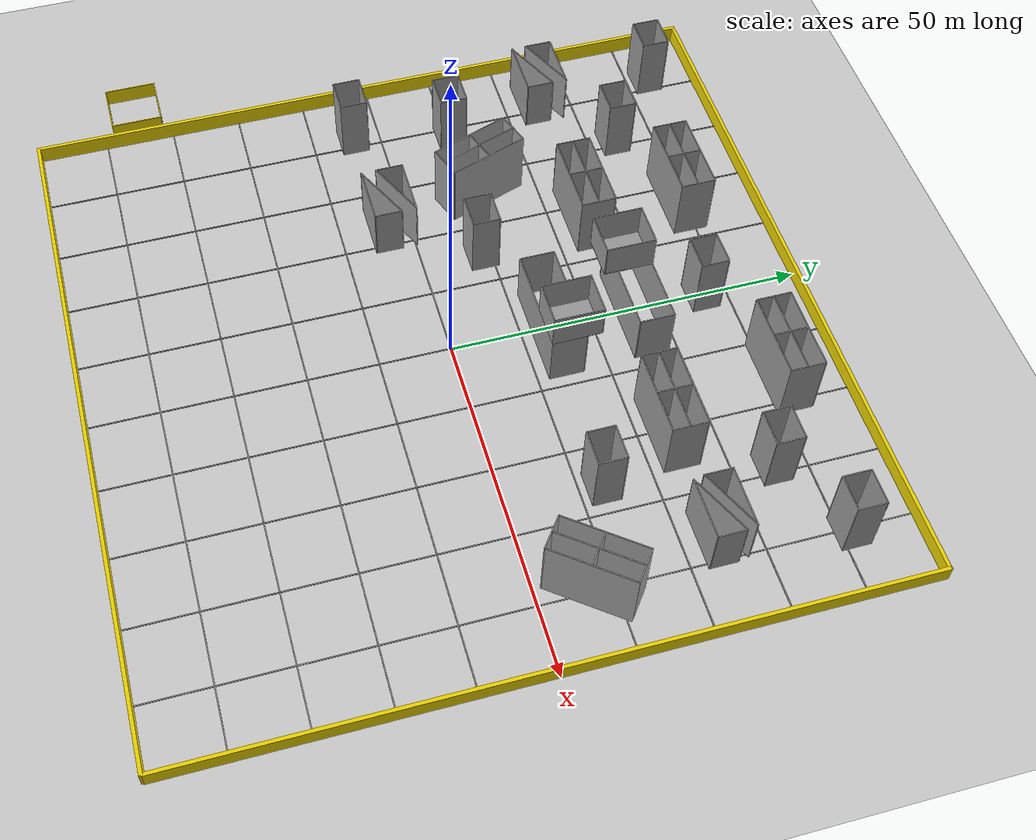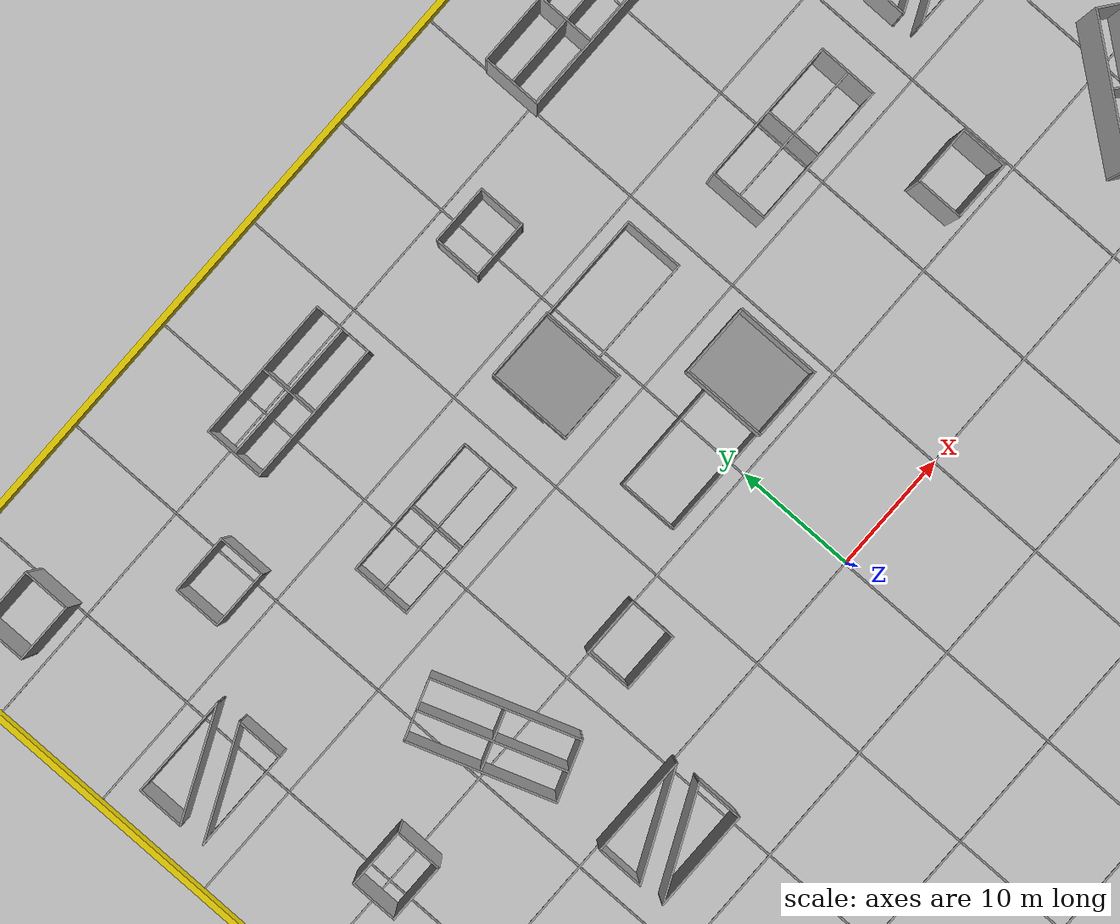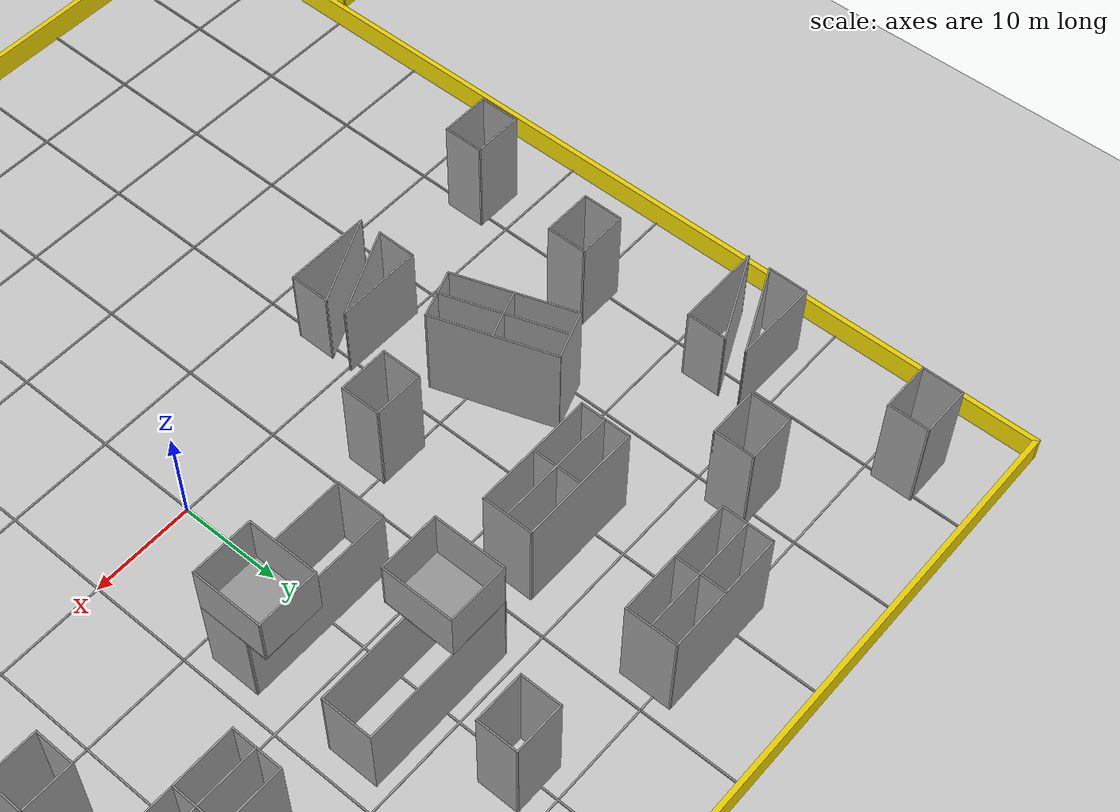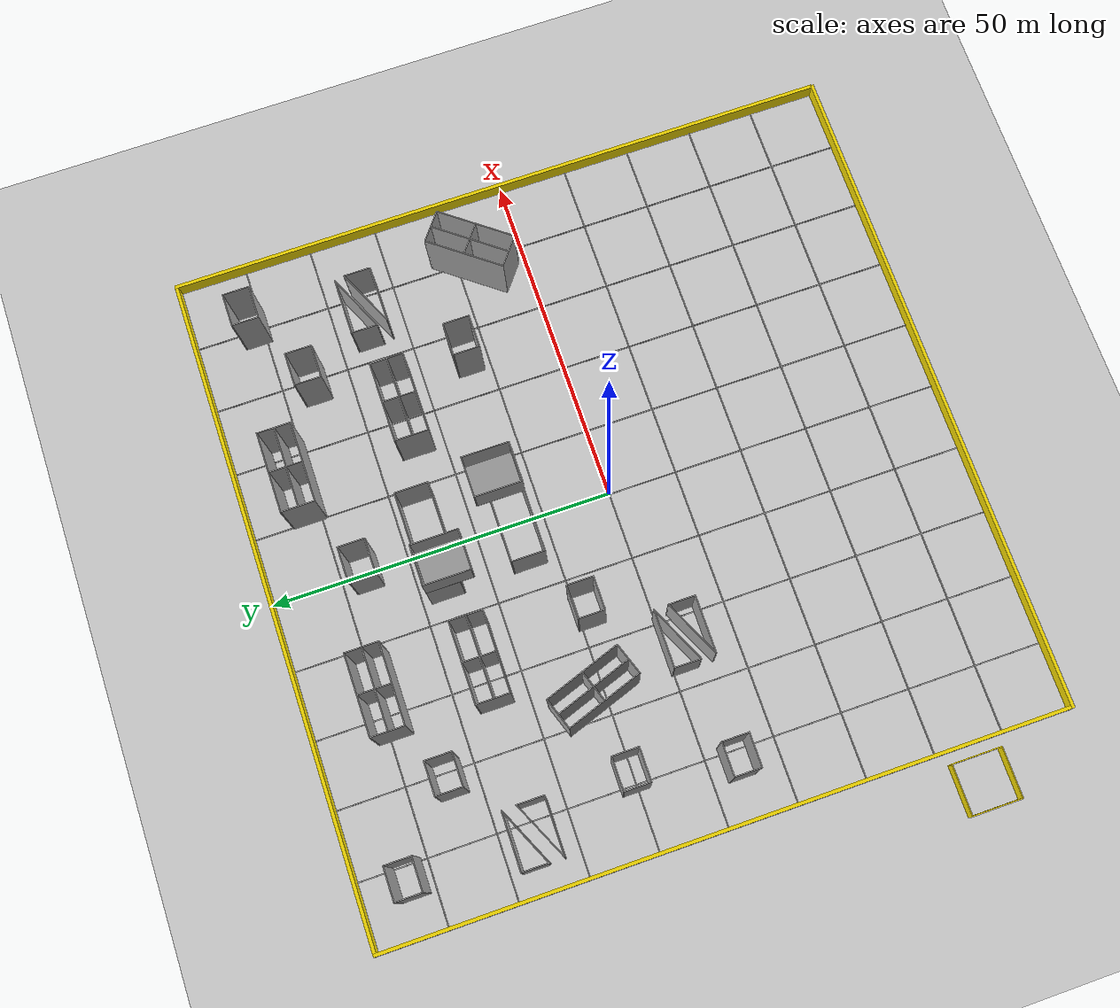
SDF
<sdf version="1.7">
 <world name="default">
  <light name="sun" type="directional">
   <pose>0 0 10 0 -0 0</pose>
   <diffuse>0.8 0.8 0.8 1</diffuse>
   <specular>0.2 0.2 0.2 1</specular>
   <attenuation>
    <range>1000</range>
    <constant>0.9</constant>
    <linear>0.01</linear>
    <quadratic>0.001</quadratic>
   </attenuation>
   <direction>-0.5 0.1 -0.9</direction>
   <spot><inner_angle>0</inner_angle><outer_angle>0</outer_angle><falloff>0</falloff></spot>
  </light>
  <model name="ground_plane">
   <static>1</static>
   <link name="link">
    <collision name="collision">
     <geometry><plane><normal>0 0 1</normal><size>100 100</size></plane></geometry>
     <surface><friction><ode><mu>100</mu><mu2>50</mu2></ode></friction></surface>
    </collision>
    <visual name="visual">
     <cast_shadows>0</cast_shadows>
     <geometry><plane><normal>0 0 1</normal><size>100 100</size></plane></geometry>
     <material>
      <script><uri>file://media/materials/scripts/gazebo.material</uri><name>Gazebo/Grey</name></script>
     </material>
    </visual>
   </link>
  </model>
  <gravity>0 0 -9.8</gravity>
  <magnetic_field>6e-06 2.3e-05 -4.2e-05</magnetic_field>
  <atmosphere type="adiabatic"/>
  <physics type="ode">
   <max_step_size>0.001</max_step_size>
   <real_time_factor>1</real_time_factor>
   <real_time_update_rate>1000</real_time_update_rate>
  </physics>
  <scene><ambient>0.4 0.4 0.4 1</ambient><background>0.7 0.7 0.7 1</background><shadows>1</shadows></scene>
  <spherical_coordinates>
   <surface_model>EARTH_WGS84</surface_model>
   <latitude_deg>0</latitude_deg>
   <longitude_deg>0</longitude_deg>
   <elevation>0</elevation>
   <heading_deg>0</heading_deg>
  </spherical_coordinates>
  <model name="gridline100m">
   <pose>0.007876 -6.97538 0 0 -0 0</pose>
   <link name="Wall_2">
    <collision name="Wall_2_Collision">
     <geometry><box><size>100 0.15 0.15</size></box></geometry>
     <pose>0 0 0.075 0 -0 0</pose>
    </collision>
    <visual name="Wall_2_Visual">
     <pose>0 0 0.075 0 -0 0</pose>
     <geometry><box><size>100 0.15 0.15</size></box></geometry>
     <material>
      <script><uri>file://media/materials/scripts/gazebo.material</uri><name>Gazebo/Grey</name></script>
      <ambient>0 0 0 1</ambient>
     </material>
     <meta><layer>0</layer></meta>
    </visual>
    <pose>2e-06 -3.05812 0 0 -0 0</pose>
   </link>
   <static>1</static>
  </model>
  <model name="gridline100m_clone">
   <pose>0.013 3.08479 0 0 -0 0</pose>
   <link name="Wall_2">
    <collision name="Wall_2_Collision">
     <geometry><box><size>100 0.15 0.15</size></box></geometry>
     <pose>0 0 0.075 0 -0 0</pose>
    </collision>
    <visual name="Wall_2_Visual">
     <pose>0 0 0.075 0 -0 0</pose>
     <geometry><box><size>100 0.15 0.15</size></box></geometry>
     <material>
      <script><uri>file://media/materials/scripts/gazebo.material</uri><name>Gazebo/Grey</name></script>
      <ambient>0 0 0 1</ambient>
     </material>
     <meta><layer>0</layer></meta>
    </visual>
    <pose>2e-06 -3.05812 0 0 -0 0</pose>
   </link>
   <static>1</static>
  </model>
  <model name="gridline100m_clone_0">
   <pose>-0.011254 13.0129 0 0 -0 0</pose>
   <link name="Wall_2">
    <collision name="Wall_2_Collision">
     <geometry><box><size>100 0.15 0.15</size></box></geometry>
     <pose>0 0 0.075 0 -0 0</pose>
    </collision>
    <visual name="Wall_2_Visual">
     <pose>0 0 0.075 0 -0 0</pose>
     <geometry><box><size>100 0.15 0.15</size></box></geometry>
     <material>
      <script><uri>file://media/materials/scripts/gazebo.material</uri><name>Gazebo/Grey</name></script>
      <ambient>0 0 0 1</ambient>
     </material>
     <meta><layer>0</layer></meta>
    </visual>
    <pose>2e-06 -3.05812 0 0 -0 0</pose>
   </link>
   <static>1</static>
  </model>
  <model name="gridline100m_clone_0_clone">
   <link name="Wall_2">
    <pose>2e-06 -3.05812 0 0 -0 1.571</pose>
    <inertial>
     <mass>1</mass>
     <inertia><ixx>1</ixx><ixy>0</ixy><ixz>0</ixz><iyy>1</iyy><iyz>0</iyz><izz>1</izz></inertia>
    </inertial>
    <visual name="Wall_2_Visual">
     <pose>0 0 0.075 0 -0 0</pose>
     <geometry><box><size>100 0.15 0.15</size></box></geometry>
     <material>
      <script><uri>file://media/materials/scripts/gazebo.material</uri><name>Gazebo/Grey</name></script>
      <ambient>0 0 0 1</ambient>
      <shader type="pixel"><normal_map>__default__</normal_map></shader>
      <diffuse>0.7 0.7 0.7 1</diffuse>
      <specular>0.01 0.01 0.01 1</specular>
      <emissive>0 0 0 1</emissive>
     </material>
     <meta><layer>0</layer></meta>
    </visual>
    <collision name="Wall_2_Collision">
     <pose>0 0 0.075 0 -0 0</pose>
     <geometry><box><size>100 0.15 0.15</size></box></geometry>
     <surface>
      <friction>
       <ode><mu>1</mu><mu2>1</mu2><fdir1>0 0 0</fdir1><slip1>0</slip1><slip2>0</slip2></ode>
       <torsional>
        <coefficient>1</coefficient>
        <patch_radius>0</patch_radius>
        <surface_radius>0</surface_radius>
        <use_patch_radius>1</use_patch_radius>
        <ode><slip>0</slip></ode>
       </torsional>
      </friction>
      <bounce><restitution_coefficient>0</restitution_coefficient><threshold>1e+06</threshold></bounce>
      <contact>
       <collide_without_contact>0</collide_without_contact>
       <collide_without_contact_bitmask>1</collide_without_contact_bitmask>
       <collide_bitmask>1</collide_bitmask>
       <ode>
        <soft_cfm>0</soft_cfm>
        <soft_erp>0.2</soft_erp>
        <kp>1e+13</kp>
        <kd>1</kd>
        <max_vel>0.01</max_vel>
        <min_depth>0</min_depth>
       </ode>
       <bullet>
        <split_impulse>1</split_impulse>
        <split_impulse_penetration_threshold>-0.01</split_impulse_penetration_threshold>
        <soft_cfm>0</soft_cfm>
        <soft_erp>0.2</soft_erp>
        <kp>1e+13</kp>
        <kd>1</kd>
       </bullet>
      </contact>
     </surface>
    </collision>
   </link>
   <static>1</static>
   <pose>9.93727 3.17557 0 0 -0 0</pose>
  </model>
  <model name="gridline100m_clone_0_clone_clone">
   <link name="Wall_2">
    <pose>2e-06 -3.05812 0 0 -0 1.571</pose>
    <inertial>
     <mass>1</mass>
     <inertia><ixx>1</ixx><ixy>0</ixy><ixz>0</ixz><iyy>1</iyy><iyz>0</iyz><izz>1</izz></inertia>
    </inertial>
    <visual name="Wall_2_Visual">
     <pose>0 0 0.075 0 -0 0</pose>
     <geometry><box><size>100 0.15 0.15</size></box></geometry>
     <material>
      <script><uri>file://media/materials/scripts/gazebo.material</uri><name>Gazebo/Grey</name></script>
      <ambient>0 0 0 1</ambient>
      <shader type="pixel"><normal_map>__default__</normal_map></shader>
      <diffuse>0.7 0.7 0.7 1</diffuse>
      <specular>0.01 0.01 0.01 1</specular>
      <emissive>0 0 0 1</emissive>
     </material>
     <meta><layer>0</layer></meta>
    </visual>
    <collision name="Wall_2_Collision">
     <pose>0 0 0.075 0 -0 0</pose>
     <geometry><box><size>100 0.15 0.15</size></box></geometry>
     <surface>
      <friction>
       <ode><mu>1</mu><mu2>1</mu2><fdir1>0 0 0</fdir1><slip1>0</slip1><slip2>0</slip2></ode>
       <torsional>
        <coefficient>1</coefficient>
        <patch_radius>0</patch_radius>
        <surface_radius>0</surface_radius>
        <use_patch_radius>1</use_patch_radius>
        <ode><slip>0</slip></ode>
       </torsional>
      </friction>
      <bounce><restitution_coefficient>0</restitution_coefficient><threshold>1e+06</threshold></bounce>
      <contact>
       <collide_without_contact>0</collide_without_contact>
       <collide_without_contact_bitmask>1</collide_without_contact_bitmask>
       <collide_bitmask>1</collide_bitmask>
       <ode>
        <soft_cfm>0</soft_cfm>
        <soft_erp>0.2</soft_erp>
        <kp>1e+13</kp>
        <kd>1</kd>
        <max_vel>0.01</max_vel>
        <min_depth>0</min_depth>
       </ode>
       <bullet>
        <split_impulse>1</split_impulse>
        <split_impulse_penetration_threshold>-0.01</split_impulse_penetration_threshold>
        <soft_cfm>0</soft_cfm>
        <soft_erp>0.2</soft_erp>
        <kp>1e+13</kp>
        <kd>1</kd>
       </bullet>
      </contact>
     </surface>
    </collision>
   </link>
   <static>1</static>
   <pose>-0.08355 3.18147 0 0 -0 0</pose>
  </model>
  <model name="gridline100m_clone_0_clone_clone_0">
   <link name="Wall_2">
    <pose>2e-06 -3.05812 0 0 -0 1.571</pose>
    <inertial>
     <mass>1</mass>
     <inertia><ixx>1</ixx><ixy>0</ixy><ixz>0</ixz><iyy>1</iyy><iyz>0</iyz><izz>1</izz></inertia>
    </inertial>
    <visual name="Wall_2_Visual">
     <pose>0 0 0.075 0 -0 0</pose>
     <geometry><box><size>100 0.15 0.15</size></box></geometry>
     <material>
      <script><uri>file://media/materials/scripts/gazebo.material</uri><name>Gazebo/Grey</name></script>
      <ambient>0 0 0 1</ambient>
      <shader type="pixel"><normal_map>__default__</normal_map></shader>
      <diffuse>0.7 0.7 0.7 1</diffuse>
      <specular>0.01 0.01 0.01 1</specular>
      <emissive>0 0 0 1</emissive>
     </material>
     <meta><layer>0</layer></meta>
    </visual>
    <collision name="Wall_2_Collision">
     <pose>0 0 0.075 0 -0 0</pose>
     <geometry><box><size>100 0.15 0.15</size></box></geometry>
     <surface>
      <friction>
       <ode><mu>1</mu><mu2>1</mu2><fdir1>0 0 0</fdir1><slip1>0</slip1><slip2>0</slip2></ode>
       <torsional>
        <coefficient>1</coefficient>
        <patch_radius>0</patch_radius>
        <surface_radius>0</surface_radius>
        <use_patch_radius>1</use_patch_radius>
        <ode><slip>0</slip></ode>
       </torsional>
      </friction>
      <bounce><restitution_coefficient>0</restitution_coefficient><threshold>1e+06</threshold></bounce>
      <contact>
       <collide_without_contact>0</collide_without_contact>
       <collide_without_contact_bitmask>1</collide_without_contact_bitmask>
       <collide_bitmask>1</collide_bitmask>
       <ode>
        <soft_cfm>0</soft_cfm>
        <soft_erp>0.2</soft_erp>
        <kp>1e+13</kp>
        <kd>1</kd>
        <max_vel>0.01</max_vel>
        <min_depth>0</min_depth>
       </ode>
       <bullet>
        <split_impulse>1</split_impulse>
        <split_impulse_penetration_threshold>-0.01</split_impulse_penetration_threshold>
        <soft_cfm>0</soft_cfm>
        <soft_erp>0.2</soft_erp>
        <kp>1e+13</kp>
        <kd>1</kd>
       </bullet>
      </contact>
     </surface>
    </collision>
   </link>
   <static>1</static>
   <pose>-9.96377 3.09569 0 0 -0 0</pose>
  </model>
  <model name="gridline100m_clone_0_clone_clone_1">
   <link name="Wall_2">
    <pose>2e-06 -3.05812 0 0 -0 1.571</pose>
    <inertial>
     <mass>1</mass>
     <inertia><ixx>1</ixx><ixy>0</ixy><ixz>0</ixz><iyy>1</iyy><iyz>0</iyz><izz>1</izz></inertia>
    </inertial>
    <visual name="Wall_2_Visual">
     <pose>0 0 0.075 0 -0 0</pose>
     <geometry><box><size>100 0.15 0.15</size></box></geometry>
     <material>
      <script><uri>file://media/materials/scripts/gazebo.material</uri><name>Gazebo/Grey</name></script>
      <ambient>0 0 0 1</ambient>
      <shader type="pixel"><normal_map>__default__</normal_map></shader>
      <diffuse>0.7 0.7 0.7 1</diffuse>
      <specular>0.01 0.01 0.01 1</specular>
      <emissive>0 0 0 1</emissive>
     </material>
     <meta><layer>0</layer></meta>
    </visual>
    <collision name="Wall_2_Collision">
     <pose>0 0 0.075 0 -0 0</pose>
     <geometry><box><size>100 0.15 0.15</size></box></geometry>
     <surface>
      <friction>
       <ode><mu>1</mu><mu2>1</mu2><fdir1>0 0 0</fdir1><slip1>0</slip1><slip2>0</slip2></ode>
       <torsional>
        <coefficient>1</coefficient>
        <patch_radius>0</patch_radius>
        <surface_radius>0</surface_radius>
        <use_patch_radius>1</use_patch_radius>
        <ode><slip>0</slip></ode>
       </torsional>
      </friction>
      <bounce><restitution_coefficient>0</restitution_coefficient><threshold>1e+06</threshold></bounce>
      <contact>
       <collide_without_contact>0</collide_without_contact>
       <collide_without_contact_bitmask>1</collide_without_contact_bitmask>
       <collide_bitmask>1</collide_bitmask>
       <ode>
        <soft_cfm>0</soft_cfm>
        <soft_erp>0.2</soft_erp>
        <kp>1e+13</kp>
        <kd>1</kd>
        <max_vel>0.01</max_vel>
        <min_depth>0</min_depth>
       </ode>
       <bullet>
        <split_impulse>1</split_impulse>
        <split_impulse_penetration_threshold>-0.01</split_impulse_penetration_threshold>
        <soft_cfm>0</soft_cfm>
        <soft_erp>0.2</soft_erp>
        <kp>1e+13</kp>
        <kd>1</kd>
       </bullet>
      </contact>
     </surface>
    </collision>
   </link>
   <static>1</static>
   <pose>20.1147 3.10463 0 0 -0 0</pose>
  </model>
  <model name="gridline100m_clone_0_clone_clone_1_clone">
   <link name="Wall_2">
    <pose>2e-06 -3.05812 0 0 -0 1.571</pose>
    <inertial>
     <mass>1</mass>
     <inertia><ixx>1</ixx><ixy>0</ixy><ixz>0</ixz><iyy>1</iyy><iyz>0</iyz><izz>1</izz></inertia>
    </inertial>
    <visual name="Wall_2_Visual">
     <pose>0 0 0.075 0 -0 0</pose>
     <geometry><box><size>100 0.15 0.15</size></box></geometry>
     <material>
      <script><uri>file://media/materials/scripts/gazebo.material</uri><name>Gazebo/Grey</name></script>
      <ambient>0 0 0 1</ambient>
      <shader type="pixel"><normal_map>__default__</normal_map></shader>
      <diffuse>0.7 0.7 0.7 1</diffuse>
      <specular>0.01 0.01 0.01 1</specular>
      <emissive>0 0 0 1</emissive>
     </material>
     <meta><layer>0</layer></meta>
    </visual>
    <collision name="Wall_2_Collision">
     <pose>0 0 0.075 0 -0 0</pose>
     <geometry><box><size>100 0.15 0.15</size></box></geometry>
     <surface>
      <friction>
       <ode><mu>1</mu><mu2>1</mu2><fdir1>0 0 0</fdir1><slip1>0</slip1><slip2>0</slip2></ode>
       <torsional>
        <coefficient>1</coefficient>
        <patch_radius>0</patch_radius>
        <surface_radius>0</surface_radius>
        <use_patch_radius>1</use_patch_radius>
        <ode><slip>0</slip></ode>
       </torsional>
      </friction>
      <bounce><restitution_coefficient>0</restitution_coefficient><threshold>1e+06</threshold></bounce>
      <contact>
       <collide_without_contact>0</collide_without_contact>
       <collide_without_contact_bitmask>1</collide_without_contact_bitmask>
       <collide_bitmask>1</collide_bitmask>
       <ode>
        <soft_cfm>0</soft_cfm>
        <soft_erp>0.2</soft_erp>
        <kp>1e+13</kp>
        <kd>1</kd>
        <max_vel>0.01</max_vel>
        <min_depth>0</min_depth>
       </ode>
       <bullet>
        <split_impulse>1</split_impulse>
        <split_impulse_penetration_threshold>-0.01</split_impulse_penetration_threshold>
        <soft_cfm>0</soft_cfm>
        <soft_erp>0.2</soft_erp>
        <kp>1e+13</kp>
        <kd>1</kd>
       </bullet>
      </contact>
     </surface>
    </collision>
   </link>
   <static>1</static>
   <pose>30.2145 3.13489 0 0 -0 0</pose>
  </model>
  <model name="gridline100m_clone_0_clone_clone_1_clone_clone">
   <link name="Wall_2">
    <pose>2e-06 -3.05812 0 0 -0 1.571</pose>
    <inertial>
     <mass>1</mass>
     <inertia><ixx>1</ixx><ixy>0</ixy><ixz>0</ixz><iyy>1</iyy><iyz>0</iyz><izz>1</izz></inertia>
    </inertial>
    <visual name="Wall_2_Visual">
     <pose>0 0 0.075 0 -0 0</pose>
     <geometry><box><size>100 0.15 0.15</size></box></geometry>
     <material>
      <script><uri>file://media/materials/scripts/gazebo.material</uri><name>Gazebo/Grey</name></script>
      <ambient>0 0 0 1</ambient>
      <shader type="pixel"><normal_map>__default__</normal_map></shader>
      <diffuse>0.7 0.7 0.7 1</diffuse>
      <specular>0.01 0.01 0.01 1</specular>
      <emissive>0 0 0 1</emissive>
     </material>
     <meta><layer>0</layer></meta>
    </visual>
    <collision name="Wall_2_Collision">
     <pose>0 0 0.075 0 -0 0</pose>
     <geometry><box><size>100 0.15 0.15</size></box></geometry>
     <surface>
      <friction>
       <ode><mu>1</mu><mu2>1</mu2><fdir1>0 0 0</fdir1><slip1>0</slip1><slip2>0</slip2></ode>
       <torsional>
        <coefficient>1</coefficient>
        <patch_radius>0</patch_radius>
        <surface_radius>0</surface_radius>
        <use_patch_radius>1</use_patch_radius>
        <ode><slip>0</slip></ode>
       </torsional>
      </friction>
      <bounce><restitution_coefficient>0</restitution_coefficient><threshold>1e+06</threshold></bounce>
      <contact>
       <collide_without_contact>0</collide_without_contact>
       <collide_without_contact_bitmask>1</collide_without_contact_bitmask>
       <collide_bitmask>1</collide_bitmask>
       <ode>
        <soft_cfm>0</soft_cfm>
        <soft_erp>0.2</soft_erp>
        <kp>1e+13</kp>
        <kd>1</kd>
        <max_vel>0.01</max_vel>
        <min_depth>0</min_depth>
       </ode>
       <bullet>
        <split_impulse>1</split_impulse>
        <split_impulse_penetration_threshold>-0.01</split_impulse_penetration_threshold>
        <soft_cfm>0</soft_cfm>
        <soft_erp>0.2</soft_erp>
        <kp>1e+13</kp>
        <kd>1</kd>
       </bullet>
      </contact>
     </surface>
    </collision>
   </link>
   <static>1</static>
   <pose>40.3256 3.07649 0 0 -0 0</pose>
  </model>
  <model name="gridline100m_clone_0_clone_clone_0_clone">
   <link name="Wall_2">
    <pose>2e-06 -3.05812 0 0 -0 1.571</pose>
    <inertial>
     <mass>1</mass>
     <inertia><ixx>1</ixx><ixy>0</ixy><ixz>0</ixz><iyy>1</iyy><iyz>0</iyz><izz>1</izz></inertia>
    </inertial>
    <visual name="Wall_2_Visual">
     <pose>0 0 0.075 0 -0 0</pose>
     <geometry><box><size>100 0.15 0.15</size></box></geometry>
     <material>
      <script><uri>file://media/materials/scripts/gazebo.material</uri><name>Gazebo/Grey</name></script>
      <ambient>0 0 0 1</ambient>
      <shader type="pixel"><normal_map>__default__</normal_map></shader>
      <diffuse>0.7 0.7 0.7 1</diffuse>
      <specular>0.01 0.01 0.01 1</specular>
      <emissive>0 0 0 1</emissive>
     </material>
     <meta><layer>0</layer></meta>
    </visual>
    <collision name="Wall_2_Collision">
     <pose>0 0 0.075 0 -0 0</pose>
     <geometry><box><size>100 0.15 0.15</size></box></geometry>
     <surface>
      <friction>
       <ode><mu>1</mu><mu2>1</mu2><fdir1>0 0 0</fdir1><slip1>0</slip1><slip2>0</slip2></ode>
       <torsional>
        <coefficient>1</coefficient>
        <patch_radius>0</patch_radius>
        <surface_radius>0</surface_radius>
        <use_patch_radius>1</use_patch_radius>
        <ode><slip>0</slip></ode>
       </torsional>
      </friction>
      <bounce><restitution_coefficient>0</restitution_coefficient><threshold>1e+06</threshold></bounce>
      <contact>
       <collide_without_contact>0</collide_without_contact>
       <collide_without_contact_bitmask>1</collide_without_contact_bitmask>
       <collide_bitmask>1</collide_bitmask>
       <ode>
        <soft_cfm>0</soft_cfm>
        <soft_erp>0.2</soft_erp>
        <kp>1e+13</kp>
        <kd>1</kd>
        <max_vel>0.01</max_vel>
        <min_depth>0</min_depth>
       </ode>
       <bullet>
        <split_impulse>1</split_impulse>
        <split_impulse_penetration_threshold>-0.01</split_impulse_penetration_threshold>
        <soft_cfm>0</soft_cfm>
        <soft_erp>0.2</soft_erp>
        <kp>1e+13</kp>
        <kd>1</kd>
       </bullet>
      </contact>
     </surface>
    </collision>
   </link>
   <static>1</static>
   <pose>-20.0665 3.08574 0 0 -0 0</pose>
  </model>
  <model name="gridline100m_clone_0_clone_clone_0_clone_clone">
   <link name="Wall_2">
    <pose>2e-06 -3.05812 0 0 -0 1.571</pose>
    <inertial>
     <mass>1</mass>
     <inertia><ixx>1</ixx><ixy>0</ixy><ixz>0</ixz><iyy>1</iyy><iyz>0</iyz><izz>1</izz></inertia>
    </inertial>
    <visual name="Wall_2_Visual">
     <pose>0 0 0.075 0 -0 0</pose>
     <geometry><box><size>100 0.15 0.15</size></box></geometry>
     <material>
      <script><uri>file://media/materials/scripts/gazebo.material</uri><name>Gazebo/Grey</name></script>
      <ambient>0 0 0 1</ambient>
      <shader type="pixel"><normal_map>__default__</normal_map></shader>
      <diffuse>0.7 0.7 0.7 1</diffuse>
      <specular>0.01 0.01 0.01 1</specular>
      <emissive>0 0 0 1</emissive>
     </material>
     <meta><layer>0</layer></meta>
    </visual>
    <collision name="Wall_2_Collision">
     <pose>0 0 0.075 0 -0 0</pose>
     <geometry><box><size>100 0.15 0.15</size></box></geometry>
     <surface>
      <friction>
       <ode><mu>1</mu><mu2>1</mu2><fdir1>0 0 0</fdir1><slip1>0</slip1><slip2>0</slip2></ode>
       <torsional>
        <coefficient>1</coefficient>
        <patch_radius>0</patch_radius>
        <surface_radius>0</surface_radius>
        <use_patch_radius>1</use_patch_radius>
        <ode><slip>0</slip></ode>
       </torsional>
      </friction>
      <bounce><restitution_coefficient>0</restitution_coefficient><threshold>1e+06</threshold></bounce>
      <contact>
       <collide_without_contact>0</collide_without_contact>
       <collide_without_contact_bitmask>1</collide_without_contact_bitmask>
       <collide_bitmask>1</collide_bitmask>
       <ode>
        <soft_cfm>0</soft_cfm>
        <soft_erp>0.2</soft_erp>
        <kp>1e+13</kp>
        <kd>1</kd>
        <max_vel>0.01</max_vel>
        <min_depth>0</min_depth>
       </ode>
       <bullet>
        <split_impulse>1</split_impulse>
        <split_impulse_penetration_threshold>-0.01</split_impulse_penetration_threshold>
        <soft_cfm>0</soft_cfm>
        <soft_erp>0.2</soft_erp>
        <kp>1e+13</kp>
        <kd>1</kd>
       </bullet>
      </contact>
     </surface>
    </collision>
   </link>
   <static>1</static>
   <pose>-30.0159 3.12682 0 0 -0 0</pose>
  </model>
  <model name="gridline100m_clone_0_clone_clone_0_clone_clone_clone">
   <link name="Wall_2">
    <pose>2e-06 -3.05812 0 0 -0 1.571</pose>
    <inertial>
     <mass>1</mass>
     <inertia><ixx>1</ixx><ixy>0</ixy><ixz>0</ixz><iyy>1</iyy><iyz>0</iyz><izz>1</izz></inertia>
    </inertial>
    <visual name="Wall_2_Visual">
     <pose>0 0 0.075 0 -0 0</pose>
     <geometry><box><size>100 0.15 0.15</size></box></geometry>
     <material>
      <script><uri>file://media/materials/scripts/gazebo.material</uri><name>Gazebo/Grey</name></script>
      <ambient>0 0 0 1</ambient>
      <shader type="pixel"><normal_map>__default__</normal_map></shader>
      <diffuse>0.7 0.7 0.7 1</diffuse>
      <specular>0.01 0.01 0.01 1</specular>
      <emissive>0 0 0 1</emissive>
     </material>
     <meta><layer>0</layer></meta>
    </visual>
    <collision name="Wall_2_Collision">
     <pose>0 0 0.075 0 -0 0</pose>
     <geometry><box><size>100 0.15 0.15</size></box></geometry>
     <surface>
      <friction>
       <ode><mu>1</mu><mu2>1</mu2><fdir1>0 0 0</fdir1><slip1>0</slip1><slip2>0</slip2></ode>
       <torsional>
        <coefficient>1</coefficient>
        <patch_radius>0</patch_radius>
        <surface_radius>0</surface_radius>
        <use_patch_radius>1</use_patch_radius>
        <ode><slip>0</slip></ode>
       </torsional>
      </friction>
      <bounce><restitution_coefficient>0</restitution_coefficient><threshold>1e+06</threshold></bounce>
      <contact>
       <collide_without_contact>0</collide_without_contact>
       <collide_without_contact_bitmask>1</collide_without_contact_bitmask>
       <collide_bitmask>1</collide_bitmask>
       <ode>
        <soft_cfm>0</soft_cfm>
        <soft_erp>0.2</soft_erp>
        <kp>1e+13</kp>
        <kd>1</kd>
        <max_vel>0.01</max_vel>
        <min_depth>0</min_depth>
       </ode>
       <bullet>
        <split_impulse>1</split_impulse>
        <split_impulse_penetration_threshold>-0.01</split_impulse_penetration_threshold>
        <soft_cfm>0</soft_cfm>
        <soft_erp>0.2</soft_erp>
        <kp>1e+13</kp>
        <kd>1</kd>
       </bullet>
      </contact>
     </surface>
    </collision>
   </link>
   <static>1</static>
   <pose>-40.0496 3.09833 0 0 -0 0</pose>
  </model>
  <model name="gridline100m_clone_1">
   <pose>-0.046986 -16.9532 0 0 -0 0</pose>
   <link name="Wall_2">
    <collision name="Wall_2_Collision">
     <geometry><box><size>100 0.15 0.15</size></box></geometry>
     <pose>0 0 0.075 0 -0 0</pose>
    </collision>
    <visual name="Wall_2_Visual">
     <pose>0 0 0.075 0 -0 0</pose>
     <geometry><box><size>100 0.15 0.15</size></box></geometry>
     <material>
      <script><uri>file://media/materials/scripts/gazebo.material</uri><name>Gazebo/Grey</name></script>
      <ambient>0 0 0 1</ambient>
     </material>
     <meta><layer>0</layer></meta>
    </visual>
    <pose>2e-06 -3.05812 0 0 -0 0</pose>
   </link>
   <static>1</static>
  </model>
  <model name="gridline100m_clone_1_clone">
   <pose>0.0391 -26.9723 0 0 -0 0</pose>
   <link name="Wall_2">
    <collision name="Wall_2_Collision">
     <geometry><box><size>100 0.15 0.15</size></box></geometry>
     <pose>0 0 0.075 0 -0 0</pose>
    </collision>
    <visual name="Wall_2_Visual">
     <pose>0 0 0.075 0 -0 0</pose>
     <geometry><box><size>100 0.15 0.15</size></box></geometry>
     <material>
      <script><uri>file://media/materials/scripts/gazebo.material</uri><name>Gazebo/Grey</name></script>
      <ambient>0 0 0 1</ambient>
     </material>
     <meta><layer>0</layer></meta>
    </visual>
    <pose>2e-06 -3.05812 0 0 -0 0</pose>
   </link>
   <static>1</static>
  </model>
  <model name="gridline100m_clone_1_clone_clone">
   <pose>-0.033098 -36.9108 0 0 -0 0</pose>
   <link name="Wall_2">
    <collision name="Wall_2_Collision">
     <geometry><box><size>100 0.15 0.15</size></box></geometry>
     <pose>0 0 0.075 0 -0 0</pose>
    </collision>
    <visual name="Wall_2_Visual">
     <pose>0 0 0.075 0 -0 0</pose>
     <geometry><box><size>100 0.15 0.15</size></box></geometry>
     <material>
      <script><uri>file://media/materials/scripts/gazebo.material</uri><name>Gazebo/Grey</name></script>
      <ambient>0 0 0 1</ambient>
     </material>
     <meta><layer>0</layer></meta>
    </visual>
    <pose>2e-06 -3.05812 0 0 -0 0</pose>
   </link>
   <static>1</static>
  </model>
  <model name="gridline100m_clone_0_clone_0">
   <pose>-0.012985 22.9729 0 0 -0 0</pose>
   <link name="Wall_2">
    <collision name="Wall_2_Collision">
     <geometry><box><size>100 0.15 0.15</size></box></geometry>
     <pose>0 0 0.075 0 -0 0</pose>
    </collision>
    <visual name="Wall_2_Visual">
     <pose>0 0 0.075 0 -0 0</pose>
     <geometry><box><size>100 0.15 0.15</size></box></geometry>
     <material>
      <script><uri>file://media/materials/scripts/gazebo.material</uri><name>Gazebo/Grey</name></script>
      <ambient>0 0 0 1</ambient>
     </material>
     <meta><layer>0</layer></meta>
    </visual>
    <pose>2e-06 -3.05812 0 0 -0 0</pose>
   </link>
   <static>1</static>
  </model>
  <model name="gridline100m_clone_0_clone_0_clone">
   <pose>-0.008378 33.0432 0 0 -0 0</pose>
   <link name="Wall_2">
    <collision name="Wall_2_Collision">
     <geometry><box><size>100 0.15 0.15</size></box></geometry>
     <pose>0 0 0.075 0 -0 0</pose>
    </collision>
    <visual name="Wall_2_Visual">
     <pose>0 0 0.075 0 -0 0</pose>
     <geometry><box><size>100 0.15 0.15</size></box></geometry>
     <material>
      <script><uri>file://media/materials/scripts/gazebo.material</uri><name>Gazebo/Grey</name></script>
      <ambient>0 0 0 1</ambient>
     </material>
     <meta><layer>0</layer></meta>
    </visual>
    <pose>2e-06 -3.05812 0 0 -0 0</pose>
   </link>
   <static>1</static>
  </model>
  <model name="gridline100m_clone_0_clone_0_clone_clone">
   <pose>-0.009803 42.9182 0 0 -0 0</pose>
   <link name="Wall_2">
    <collision name="Wall_2_Collision">
     <geometry><box><size>100 0.15 0.15</size></box></geometry>
     <pose>0 0 0.075 0 -0 0</pose>
    </collision>
    <visual name="Wall_2_Visual">
     <pose>0 0 0.075 0 -0 0</pose>
     <geometry><box><size>100 0.15 0.15</size></box></geometry>
     <material>
      <script><uri>file://media/materials/scripts/gazebo.material</uri><name>Gazebo/Grey</name></script>
      <ambient>0 0 0 1</ambient>
     </material>
     <meta><layer>0</layer></meta>
    </visual>
    <pose>2e-06 -3.05812 0 0 -0 0</pose>
   </link>
   <static>1</static>
  </model>
  <model name="100mfence_clone">
   <link name="Wall_0">
    <pose>-2e-06 -1.2425 0 0 -0 0</pose>
    <inertial>
     <mass>1</mass>
     <inertia><ixx>1</ixx><ixy>0</ixy><ixz>0</ixz><iyy>1</iyy><iyz>0</iyz><izz>1</izz></inertia>
    </inertial>
    <visual name="Wall_0_Visual">
     <pose>0 0 1.25 0 -0 0</pose>
     <geometry><box><size>100 0.5 2.5</size></box></geometry>
     <material>
      <script><uri>file://media/materials/scripts/gazebo.material</uri><name>Gazebo/Grey</name></script>
      <ambient>0.929 0.831 0 1</ambient>
      <shader type="pixel"><normal_map>__default__</normal_map></shader>
      <diffuse>0.7 0.7 0.7 1</diffuse>
      <specular>0.01 0.01 0.01 1</specular>
      <emissive>0 0 0 1</emissive>
     </material>
     <meta><layer>0</layer></meta>
    </visual>
    <collision name="Wall_0_Collision">
     <pose>0 0 1.25 0 -0 0</pose>
     <geometry><box><size>100 0.15 2.5</size></box></geometry>
     <surface>
      <friction>
       <ode><mu>1</mu><mu2>1</mu2><fdir1>0 0 0</fdir1><slip1>0</slip1><slip2>0</slip2></ode>
       <torsional>
        <coefficient>1</coefficient>
        <patch_radius>0</patch_radius>
        <surface_radius>0</surface_radius>
        <use_patch_radius>1</use_patch_radius>
        <ode><slip>0</slip></ode>
       </torsional>
      </friction>
      <bounce><restitution_coefficient>0</restitution_coefficient><threshold>1e+06</threshold></bounce>
      <contact>
       <collide_without_contact>0</collide_without_contact>
       <collide_without_contact_bitmask>1</collide_without_contact_bitmask>
       <collide_bitmask>1</collide_bitmask>
       <ode>
        <soft_cfm>0</soft_cfm>
        <soft_erp>0.2</soft_erp>
        <kp>1e+13</kp>
        <kd>1</kd>
        <max_vel>0.01</max_vel>
        <min_depth>0</min_depth>
       </ode>
       <bullet>
        <split_impulse>1</split_impulse>
        <split_impulse_penetration_threshold>-0.01</split_impulse_penetration_threshold>
        <soft_cfm>0</soft_cfm>
        <soft_erp>0.2</soft_erp>
        <kp>1e+13</kp>
        <kd>1</kd>
       </bullet>
      </contact>
     </surface>
    </collision>
   </link>
   <static>1</static>
   <pose>0.000191 51.1672 0 0 -0 0</pose>
  </model>
  <model name="100mfence_clone_clone">
   <link name="Wall_0">
    <pose>-13.0161 -13.4589 0 0 -0 1.571</pose>
    <inertial>
     <mass>1</mass>
     <inertia><ixx>1</ixx><ixy>0</ixy><ixz>0</ixz><iyy>1</iyy><iyz>0</iyz><izz>1</izz></inertia>
    </inertial>
    <visual name="Wall_0_Visual">
     <pose>0 0 1.25 0 -0 0</pose>
     <geometry><box><size>100 0.5 2.5</size></box></geometry>
     <material>
      <script><uri>file://media/materials/scripts/gazebo.material</uri><name>Gazebo/Grey</name></script>
      <ambient>0.929 0.831 0 1</ambient>
      <shader type="pixel"><normal_map>__default__</normal_map></shader>
      <diffuse>0.7 0.7 0.7 1</diffuse>
      <specular>0.01 0.01 0.01 1</specular>
      <emissive>0 0 0 1</emissive>
     </material>
     <meta><layer>0</layer></meta>
    </visual>
    <collision name="Wall_0_Collision">
     <pose>0 0 1.25 0 -0 0</pose>
     <geometry><box><size>100 0.15 2.5</size></box></geometry>
     <surface>
      <friction>
       <ode><mu>1</mu><mu2>1</mu2><fdir1>0 0 0</fdir1><slip1>0</slip1><slip2>0</slip2></ode>
       <torsional>
        <coefficient>1</coefficient>
        <patch_radius>0</patch_radius>
        <surface_radius>0</surface_radius>
        <use_patch_radius>1</use_patch_radius>
        <ode><slip>0</slip></ode>
       </torsional>
      </friction>
      <bounce><restitution_coefficient>0</restitution_coefficient><threshold>1e+06</threshold></bounce>
      <contact>
       <collide_without_contact>0</collide_without_contact>
       <collide_without_contact_bitmask>1</collide_without_contact_bitmask>
       <collide_bitmask>1</collide_bitmask>
       <ode>
        <soft_cfm>0</soft_cfm>
        <soft_erp>0.2</soft_erp>
        <kp>1e+13</kp>
        <kd>1</kd>
        <max_vel>0.01</max_vel>
        <min_depth>0</min_depth>
       </ode>
       <bullet>
        <split_impulse>1</split_impulse>
        <split_impulse_penetration_threshold>-0.01</split_impulse_penetration_threshold>
        <soft_cfm>0</soft_cfm>
        <soft_erp>0.2</soft_erp>
        <kp>1e+13</kp>
        <kd>1</kd>
       </bullet>
      </contact>
     </surface>
    </collision>
   </link>
   <static>1</static>
   <pose>-36.7919 13.635 0 0 -0 0</pose>
  </model>
  <model name="100mfence">
   <link name="Wall_0">
    <pose>-2e-06 -1.2425 0 0 -0 0</pose>
    <inertial>
     <mass>1</mass>
     <inertia><ixx>1</ixx><ixy>0</ixy><ixz>0</ixz><iyy>1</iyy><iyz>0</iyz><izz>1</izz></inertia>
    </inertial>
    <visual name="Wall_0_Visual">
     <pose>0 0 1.25 0 -0 0</pose>
     <geometry><box><size>100 0.5 2.5</size></box></geometry>
     <material>
      <script><uri>file://media/materials/scripts/gazebo.material</uri><name>Gazebo/Grey</name></script>
      <ambient>0.929 0.831 0 1</ambient>
      <shader type="pixel"><normal_map>__default__</normal_map></shader>
      <diffuse>0.7 0.7 0.7 1</diffuse>
      <specular>0.01 0.01 0.01 1</specular>
      <emissive>0 0 0 1</emissive>
     </material>
     <meta><layer>0</layer></meta>
    </visual>
    <collision name="Wall_0_Collision">
     <pose>0 0 1.25 0 -0 0</pose>
     <geometry><box><size>100 0.15 2.5</size></box></geometry>
     <surface>
      <friction>
       <ode><mu>1</mu><mu2>1</mu2><fdir1>0 0 0</fdir1><slip1>0</slip1><slip2>0</slip2></ode>
       <torsional>
        <coefficient>1</coefficient>
        <patch_radius>0</patch_radius>
        <surface_radius>0</surface_radius>
        <use_patch_radius>1</use_patch_radius>
        <ode><slip>0</slip></ode>
       </torsional>
      </friction>
      <bounce><restitution_coefficient>0</restitution_coefficient><threshold>1e+06</threshold></bounce>
      <contact>
       <collide_without_contact>0</collide_without_contact>
       <collide_without_contact_bitmask>1</collide_without_contact_bitmask>
       <collide_bitmask>1</collide_bitmask>
       <ode>
        <soft_cfm>0</soft_cfm>
        <soft_erp>0.2</soft_erp>
        <kp>1e+13</kp>
        <kd>1</kd>
        <max_vel>0.01</max_vel>
        <min_depth>0</min_depth>
       </ode>
       <bullet>
        <split_impulse>1</split_impulse>
        <split_impulse_penetration_threshold>-0.01</split_impulse_penetration_threshold>
        <soft_cfm>0</soft_cfm>
        <soft_erp>0.2</soft_erp>
        <kp>1e+13</kp>
        <kd>1</kd>
       </bullet>
      </contact>
     </surface>
    </collision>
   </link>
   <static>1</static>
   <pose>-0.048199 -48.6494 0 0 -0 0</pose>
  </model>
  <model name="100mfence_clone_clone_clone">
   <link name="Wall_0">
    <pose>-13.0161 -13.4589 0 0 -0 1.571</pose>
    <inertial>
     <mass>75000</mass>
     <inertia>
      <ixx>39203.1</ixx>
      <ixy>0</ixy>
      <ixz>0</ixz>
      <iyy>6.25391e+07</iyy>
      <iyz>0</iyz>
      <izz>6.25001e+07</izz>
     </inertia>
    </inertial>
    <visual name="Wall_0_Visual">
     <pose>0 0 1.25 0 -0 0</pose>
     <geometry><box><size>100 0.5 2.5</size></box></geometry>
     <material>
      <script><uri>file://media/materials/scripts/gazebo.material</uri><name>Gazebo/Grey</name></script>
      <ambient>0.929 0.831 0 1</ambient>
      <shader type="pixel"><normal_map>__default__</normal_map></shader>
      <diffuse>0.7 0.7 0.7 1</diffuse>
      <specular>0.01 0.01 0.01 1</specular>
      <emissive>0 0 0 1</emissive>
     </material>
     <meta><layer>0</layer></meta>
    </visual>
    <collision name="Wall_0_Collision">
     <pose>0 0 1.25 0 -0 0</pose>
     <geometry><box><size>100 0.2 2.5</size></box></geometry>
     <surface>
      <friction>
       <ode><mu>1</mu><mu2>1</mu2><fdir1>0 0 0</fdir1><slip1>0</slip1><slip2>0</slip2></ode>
       <torsional>
        <coefficient>1</coefficient>
        <patch_radius>0</patch_radius>
        <surface_radius>0</surface_radius>
        <use_patch_radius>1</use_patch_radius>
        <ode><slip>0</slip></ode>
       </torsional>
      </friction>
      <bounce><restitution_coefficient>0</restitution_coefficient><threshold>1e+06</threshold></bounce>
      <contact>
       <collide_without_contact>0</collide_without_contact>
       <collide_without_contact_bitmask>1</collide_without_contact_bitmask>
       <collide_bitmask>1</collide_bitmask>
       <ode>
        <soft_cfm>0</soft_cfm>
        <soft_erp>0.2</soft_erp>
        <kp>1e+13</kp>
        <kd>1</kd>
        <max_vel>0.01</max_vel>
        <min_depth>0</min_depth>
       </ode>
       <bullet>
        <split_impulse>1</split_impulse>
        <split_impulse_penetration_threshold>-0.01</split_impulse_penetration_threshold>
        <soft_cfm>0</soft_cfm>
        <soft_erp>0.2</soft_erp>
        <kp>1e+13</kp>
        <kd>1</kd>
       </bullet>
      </contact>
     </surface>
    </collision>
   </link>
   <static>1</static>
   <pose>62.8409 13.6369 0 0 -0 0</pose>
  </model>
  <model name="building1">
   <pose>-37.3685 11.6246 0 0 -0 0</pose>
   <link name="Wall_12">
    <collision name="Wall_12_Collision">
     <geometry><box><size>5 0.15 10</size></box></geometry>
     <pose>0 0 5 0 -0 0</pose>
    </collision>
    <visual name="Wall_12_Visual">
     <pose>0 0 5 0 -0 0</pose>
     <geometry><box><size>5 0.15 10</size></box></geometry>
     <material>
      <script><uri>file://media/materials/scripts/gazebo.material</uri><name>Gazebo/Grey</name></script>
      <ambient>0 0 0 1</ambient>
     </material>
     <meta><layer>0</layer></meta>
    </visual>
    <pose>-1.19 -3.2645 0 0 -0 0</pose>
   </link>
   <link name="Wall_13">
    <collision name="Wall_13_Collision">
     <geometry><box><size>4 0.15 10</size></box></geometry>
     <pose>0 0 5 0 -0 0</pose>
    </collision>
    <visual name="Wall_13_Visual">
     <pose>0 0 5 0 -0 0</pose>
     <geometry><box><size>4 0.15 10</size></box></geometry>
     <material>
      <script><uri>file://media/materials/scripts/gazebo.material</uri><name>Gazebo/Grey</name></script>
      <ambient>0 0 0 1</ambient>
     </material>
     <meta><layer>0</layer></meta>
    </visual>
    <pose>1.235 -1.3395 0 0 -0 1.5708</pose>
   </link>
   <link name="Wall_15">
    <collision name="Wall_15_Collision">
     <geometry><box><size>5 0.15 10</size></box></geometry>
     <pose>0 0 5 0 -0 0</pose>
    </collision>
    <visual name="Wall_15_Visual">
     <pose>0 0 5 0 -0 0</pose>
     <geometry><box><size>5 0.15 10</size></box></geometry>
     <material>
      <script><uri>file://media/materials/scripts/gazebo.material</uri><name>Gazebo/Grey</name></script>
      <ambient>0 0 0 1</ambient>
     </material>
     <meta><layer>0</layer></meta>
    </visual>
    <pose>-1.19 0.5855 0 0 -0 3.14159</pose>
   </link>
   <link name="Wall_16">
    <collision name="Wall_16_Collision">
     <geometry><box><size>4 0.15 10</size></box></geometry>
     <pose>0 0 5 0 -0 0</pose>
    </collision>
    <visual name="Wall_16_Visual">
     <pose>0 0 5 0 -0 0</pose>
     <geometry><box><size>4 0.15 10</size></box></geometry>
     <material>
      <script><uri>file://media/materials/scripts/gazebo.material</uri><name>Gazebo/Grey</name></script>
      <ambient>0 0 0 1</ambient>
     </material>
     <meta><layer>0</layer></meta>
    </visual>
    <pose>-3.615 -1.3395 0 0 -0 -1.5708</pose>
   </link>
   <static>1</static>
  </model>
  <model name="building2">
   <pose>-23.4031 -2.16335 0 0 -0 0</pose>
   <link name="Wall_20">
    <collision name="Wall_20_Collision">
     <geometry><box><size>4 0.15 8</size></box></geometry>
     <pose>0 0 4 0 -0 0</pose>
    </collision>
    <visual name="Wall_20_Visual">
     <pose>0 0 4 0 -0 0</pose>
     <geometry><box><size>4 0.15 8</size></box></geometry>
     <material>
      <script><uri>file://media/materials/scripts/gazebo.material</uri><name>Gazebo/Grey</name></script>
      <ambient>0.00784314 0.00784314 0.00784314 1</ambient>
     </material>
     <meta><layer>0</layer></meta>
    </visual>
    <pose>4.175 -1.60474 0 0 -0 -1.5708</pose>
   </link>
   <link name="Wall_21">
    <collision name="Wall_21_Collision">
     <geometry><box><size>8.5 0.15 8</size></box></geometry>
     <pose>0 0 4 0 -0 0</pose>
    </collision>
    <visual name="Wall_21_Visual">
     <pose>0 0 4 0 -0 0</pose>
     <geometry><box><size>8.5 0.15 8</size></box></geometry>
     <material>
      <script><uri>file://media/materials/scripts/gazebo.material</uri><name>Gazebo/Grey</name></script>
      <ambient>0.00784314 0.00784314 0.00784314 1</ambient>
     </material>
     <meta><layer>0</layer></meta>
    </visual>
    <pose>-0 -3.52974 0 0 -0 3.14159</pose>
   </link>
   <link name="Wall_24">
    <collision name="Wall_24_Collision">
     <geometry><box><size>9.34484 0.15 8</size></box></geometry>
     <pose>0 0 4 0 -0 0</pose>
    </collision>
    <visual name="Wall_24_Visual">
     <pose>0 0 4 0 -0 0</pose>
     <geometry><box><size>9.34484 0.15 8</size></box></geometry>
     <material>
      <script><uri>file://media/materials/scripts/gazebo.material</uri><name>Gazebo/Grey</name></script>
      <ambient>0.00784314 0.00784314 0.00784314 1</ambient>
     </material>
     <meta><layer>0</layer></meta>
    </visual>
    <pose>-0 -1.60474 0 0 -0 0.432028</pose>
   </link>
   <static>1</static>
  </model>
  <model name="building2_clone">
   <pose>-23.4605 -3.22901 0 0 -0 3.13698</pose>
   <link name="Wall_20">
    <collision name="Wall_20_Collision">
     <geometry><box><size>4 0.15 8</size></box></geometry>
     <pose>0 0 4 0 -0 0</pose>
    </collision>
    <visual name="Wall_20_Visual">
     <pose>0 0 4 0 -0 0</pose>
     <geometry><box><size>4 0.15 8</size></box></geometry>
     <material>
      <script><uri>file://media/materials/scripts/gazebo.material</uri><name>Gazebo/Grey</name></script>
      <ambient>0.00784314 0.00784314 0.00784314 1</ambient>
     </material>
     <meta><layer>0</layer></meta>
    </visual>
    <pose>4.175 -1.60474 0 0 -0 -1.5708</pose>
   </link>
   <link name="Wall_21">
    <collision name="Wall_21_Collision">
     <geometry><box><size>8.5 0.15 8</size></box></geometry>
     <pose>0 0 4 0 -0 0</pose>
    </collision>
    <visual name="Wall_21_Visual">
     <pose>0 0 4 0 -0 0</pose>
     <geometry><box><size>8.5 0.15 8</size></box></geometry>
     <material>
      <script><uri>file://media/materials/scripts/gazebo.material</uri><name>Gazebo/Grey</name></script>
      <ambient>0.00784314 0.00784314 0.00784314 1</ambient>
     </material>
     <meta><layer>0</layer></meta>
    </visual>
    <pose>-0 -3.52974 0 0 -0 3.14159</pose>
   </link>
   <link name="Wall_24">
    <collision name="Wall_24_Collision">
     <geometry><box><size>9.34484 0.15 8</size></box></geometry>
     <pose>0 0 4 0 -0 0</pose>
    </collision>
    <visual name="Wall_24_Visual">
     <pose>0 0 4 0 -0 0</pose>
     <geometry><box><size>9.34484 0.15 8</size></box></geometry>
     <material>
      <script><uri>file://media/materials/scripts/gazebo.material</uri><name>Gazebo/Grey</name></script>
      <ambient>0.00784314 0.00784314 0.00784314 1</ambient>
     </material>
     <meta><layer>0</layer></meta>
    </visual>
    <pose>-0 -1.60474 0 0 -0 0.432028</pose>
   </link>
   <static>1</static>
  </model>
  <model name="building1_clone">
   <pose>-29.8796 35.0783 0 0 -0 0</pose>
   <link name="Wall_12">
    <collision name="Wall_12_Collision">
     <geometry><box><size>5 0.15 10</size></box></geometry>
     <pose>0 0 5 0 -0 0</pose>
    </collision>
    <visual name="Wall_12_Visual">
     <pose>0 0 5 0 -0 0</pose>
     <geometry><box><size>5 0.15 10</size></box></geometry>
     <material>
      <script><uri>file://media/materials/scripts/gazebo.material</uri><name>Gazebo/Grey</name></script>
      <ambient>0 0 0 1</ambient>
     </material>
     <meta><layer>0</layer></meta>
    </visual>
    <pose>-1.19 -3.2645 0 0 -0 0</pose>
   </link>
   <link name="Wall_13">
    <collision name="Wall_13_Collision">
     <geometry><box><size>4 0.15 10</size></box></geometry>
     <pose>0 0 5 0 -0 0</pose>
    </collision>
    <visual name="Wall_13_Visual">
     <pose>0 0 5 0 -0 0</pose>
     <geometry><box><size>4 0.15 10</size></box></geometry>
     <material>
      <script><uri>file://media/materials/scripts/gazebo.material</uri><name>Gazebo/Grey</name></script>
      <ambient>0 0 0 1</ambient>
     </material>
     <meta><layer>0</layer></meta>
    </visual>
    <pose>1.235 -1.3395 0 0 -0 1.5708</pose>
   </link>
   <link name="Wall_15">
    <collision name="Wall_15_Collision">
     <geometry><box><size>5 0.15 10</size></box></geometry>
     <pose>0 0 5 0 -0 0</pose>
    </collision>
    <visual name="Wall_15_Visual">
     <pose>0 0 5 0 -0 0</pose>
     <geometry><box><size>5 0.15 10</size></box></geometry>
     <material>
      <script><uri>file://media/materials/scripts/gazebo.material</uri><name>Gazebo/Grey</name></script>
      <ambient>0 0 0 1</ambient>
     </material>
     <meta><layer>0</layer></meta>
    </visual>
    <pose>-1.19 0.5855 0 0 -0 3.14159</pose>
   </link>
   <link name="Wall_16">
    <collision name="Wall_16_Collision">
     <geometry><box><size>4 0.15 10</size></box></geometry>
     <pose>0 0 5 0 -0 0</pose>
    </collision>
    <visual name="Wall_16_Visual">
     <pose>0 0 5 0 -0 0</pose>
     <geometry><box><size>4 0.15 10</size></box></geometry>
     <material>
      <script><uri>file://media/materials/scripts/gazebo.material</uri><name>Gazebo/Grey</name></script>
      <ambient>0 0 0 1</ambient>
     </material>
     <meta><layer>0</layer></meta>
    </visual>
    <pose>-3.615 -1.3395 0 0 -0 -1.5708</pose>
   </link>
   <static>1</static>
  </model>
  <model name="building1_clone_0">
   <pose>-13.8041 9.88368 0 0 -0 0</pose>
   <link name="Wall_12">
    <collision name="Wall_12_Collision">
     <geometry><box><size>5 0.15 10</size></box></geometry>
     <pose>0 0 5 0 -0 0</pose>
    </collision>
    <visual name="Wall_12_Visual">
     <pose>0 0 5 0 -0 0</pose>
     <geometry><box><size>5 0.15 10</size></box></geometry>
     <material>
      <script><uri>file://media/materials/scripts/gazebo.material</uri><name>Gazebo/Grey</name></script>
      <ambient>0 0 0 1</ambient>
     </material>
     <meta><layer>0</layer></meta>
    </visual>
    <pose>-1.19 -3.2645 0 0 -0 0</pose>
   </link>
   <link name="Wall_13">
    <collision name="Wall_13_Collision">
     <geometry><box><size>4 0.15 10</size></box></geometry>
     <pose>0 0 5 0 -0 0</pose>
    </collision>
    <visual name="Wall_13_Visual">
     <pose>0 0 5 0 -0 0</pose>
     <geometry><box><size>4 0.15 10</size></box></geometry>
     <material>
      <script><uri>file://media/materials/scripts/gazebo.material</uri><name>Gazebo/Grey</name></script>
      <ambient>0 0 0 1</ambient>
     </material>
     <meta><layer>0</layer></meta>
    </visual>
    <pose>1.235 -1.3395 0 0 -0 1.5708</pose>
   </link>
   <link name="Wall_15">
    <collision name="Wall_15_Collision">
     <geometry><box><size>5 0.15 10</size></box></geometry>
     <pose>0 0 5 0 -0 0</pose>
    </collision>
    <visual name="Wall_15_Visual">
     <pose>0 0 5 0 -0 0</pose>
     <geometry><box><size>5 0.15 10</size></box></geometry>
     <material>
      <script><uri>file://media/materials/scripts/gazebo.material</uri><name>Gazebo/Grey</name></script>
      <ambient>0 0 0 1</ambient>
     </material>
     <meta><layer>0</layer></meta>
    </visual>
    <pose>-1.19 0.5855 0 0 -0 3.14159</pose>
   </link>
   <link name="Wall_16">
    <collision name="Wall_16_Collision">
     <geometry><box><size>4 0.15 10</size></box></geometry>
     <pose>0 0 5 0 -0 0</pose>
    </collision>
    <visual name="Wall_16_Visual">
     <pose>0 0 5 0 -0 0</pose>
     <geometry><box><size>4 0.15 10</size></box></geometry>
     <material>
      <script><uri>file://media/materials/scripts/gazebo.material</uri><name>Gazebo/Grey</name></script>
      <ambient>0 0 0 1</ambient>
     </material>
     <meta><layer>0</layer></meta>
    </visual>
    <pose>-3.615 -1.3395 0 0 -0 -1.5708</pose>
   </link>
   <static>1</static>
  </model>
  <model name="building1_clone_1">
   <pose>-40.328 -2.68313 0 0 -0 0</pose>
   <link name="Wall_12">
    <collision name="Wall_12_Collision">
     <geometry><box><size>5 0.15 10</size></box></geometry>
     <pose>0 0 5 0 -0 0</pose>
    </collision>
    <visual name="Wall_12_Visual">
     <pose>0 0 5 0 -0 0</pose>
     <geometry><box><size>5 0.15 10</size></box></geometry>
     <material>
      <script><uri>file://media/materials/scripts/gazebo.material</uri><name>Gazebo/Grey</name></script>
      <ambient>0 0 0 1</ambient>
     </material>
     <meta><layer>0</layer></meta>
    </visual>
    <pose>-1.19 -3.2645 0 0 -0 0</pose>
   </link>
   <link name="Wall_13">
    <collision name="Wall_13_Collision">
     <geometry><box><size>4 0.15 10</size></box></geometry>
     <pose>0 0 5 0 -0 0</pose>
    </collision>
    <visual name="Wall_13_Visual">
     <pose>0 0 5 0 -0 0</pose>
     <geometry><box><size>4 0.15 10</size></box></geometry>
     <material>
      <script><uri>file://media/materials/scripts/gazebo.material</uri><name>Gazebo/Grey</name></script>
      <ambient>0 0 0 1</ambient>
     </material>
     <meta><layer>0</layer></meta>
    </visual>
    <pose>1.235 -1.3395 0 0 -0 1.5708</pose>
   </link>
   <link name="Wall_15">
    <collision name="Wall_15_Collision">
     <geometry><box><size>5 0.15 10</size></box></geometry>
     <pose>0 0 5 0 -0 0</pose>
    </collision>
    <visual name="Wall_15_Visual">
     <pose>0 0 5 0 -0 0</pose>
     <geometry><box><size>5 0.15 10</size></box></geometry>
     <material>
      <script><uri>file://media/materials/scripts/gazebo.material</uri><name>Gazebo/Grey</name></script>
      <ambient>0 0 0 1</ambient>
     </material>
     <meta><layer>0</layer></meta>
    </visual>
    <pose>-1.19 0.5855 0 0 -0 3.14159</pose>
   </link>
   <link name="Wall_16">
    <collision name="Wall_16_Collision">
     <geometry><box><size>4 0.15 10</size></box></geometry>
     <pose>0 0 5 0 -0 0</pose>
    </collision>
    <visual name="Wall_16_Visual">
     <pose>0 0 5 0 -0 0</pose>
     <geometry><box><size>4 0.15 10</size></box></geometry>
     <material>
      <script><uri>file://media/materials/scripts/gazebo.material</uri><name>Gazebo/Grey</name></script>
      <ambient>0 0 0 1</ambient>
     </material>
     <meta><layer>0</layer></meta>
    </visual>
    <pose>-3.615 -1.3395 0 0 -0 -1.5708</pose>
   </link>
   <static>1</static>
  </model>
  <model name="building2_clone_0">
   <pose>-42.0321 25.7087 0 0 -0 0</pose>
   <link name="Wall_20">
    <collision name="Wall_20_Collision">
     <geometry><box><size>4 0.15 8</size></box></geometry>
     <pose>0 0 4 0 -0 0</pose>
    </collision>
    <visual name="Wall_20_Visual">
     <pose>0 0 4 0 -0 0</pose>
     <geometry><box><size>4 0.15 8</size></box></geometry>
     <material>
      <script><uri>file://media/materials/scripts/gazebo.material</uri><name>Gazebo/Grey</name></script>
      <ambient>0.00784314 0.00784314 0.00784314 1</ambient>
     </material>
     <meta><layer>0</layer></meta>
    </visual>
    <pose>4.175 -1.60474 0 0 -0 -1.5708</pose>
   </link>
   <link name="Wall_21">
    <collision name="Wall_21_Collision">
     <geometry><box><size>8.5 0.15 8</size></box></geometry>
     <pose>0 0 4 0 -0 0</pose>
    </collision>
    <visual name="Wall_21_Visual">
     <pose>0 0 4 0 -0 0</pose>
     <geometry><box><size>8.5 0.15 8</size></box></geometry>
     <material>
      <script><uri>file://media/materials/scripts/gazebo.material</uri><name>Gazebo/Grey</name></script>
      <ambient>0.00784314 0.00784314 0.00784314 1</ambient>
     </material>
     <meta><layer>0</layer></meta>
    </visual>
    <pose>-0 -3.52974 0 0 -0 3.14159</pose>
   </link>
   <link name="Wall_24">
    <collision name="Wall_24_Collision">
     <geometry><box><size>9.34484 0.15 8</size></box></geometry>
     <pose>0 0 4 0 -0 0</pose>
    </collision>
    <visual name="Wall_24_Visual">
     <pose>0 0 4 0 -0 0</pose>
     <geometry><box><size>9.34484 0.15 8</size></box></geometry>
     <material>
      <script><uri>file://media/materials/scripts/gazebo.material</uri><name>Gazebo/Grey</name></script>
      <ambient>0.00784314 0.00784314 0.00784314 1</ambient>
     </material>
     <meta><layer>0</layer></meta>
    </visual>
    <pose>-0 -1.60474 0 0 -0 0.432028</pose>
   </link>
   <static>1</static>
  </model>
  <model name="building2_clone_clone">
   <pose>-42.105 24.6316 0 0 -0 3.13698</pose>
   <link name="Wall_20">
    <collision name="Wall_20_Collision">
     <geometry><box><size>4 0.15 8</size></box></geometry>
     <pose>0 0 4 0 -0 0</pose>
    </collision>
    <visual name="Wall_20_Visual">
     <pose>0 0 4 0 -0 0</pose>
     <geometry><box><size>4 0.15 8</size></box></geometry>
     <material>
      <script><uri>file://media/materials/scripts/gazebo.material</uri><name>Gazebo/Grey</name></script>
      <ambient>0.00784314 0.00784314 0.00784314 1</ambient>
     </material>
     <meta><layer>0</layer></meta>
    </visual>
    <pose>4.175 -1.60474 0 0 -0 -1.5708</pose>
   </link>
   <link name="Wall_21">
    <collision name="Wall_21_Collision">
     <geometry><box><size>8.5 0.15 8</size></box></geometry>
     <pose>0 0 4 0 -0 0</pose>
    </collision>
    <visual name="Wall_21_Visual">
     <pose>0 0 4 0 -0 0</pose>
     <geometry><box><size>8.5 0.15 8</size></box></geometry>
     <material>
      <script><uri>file://media/materials/scripts/gazebo.material</uri><name>Gazebo/Grey</name></script>
      <ambient>0.00784314 0.00784314 0.00784314 1</ambient>
     </material>
     <meta><layer>0</layer></meta>
    </visual>
    <pose>-0 -3.52974 0 0 -0 3.14159</pose>
   </link>
   <link name="Wall_24">
    <collision name="Wall_24_Collision">
     <geometry><box><size>9.34484 0.15 8</size></box></geometry>
     <pose>0 0 4 0 -0 0</pose>
    </collision>
    <visual name="Wall_24_Visual">
     <pose>0 0 4 0 -0 0</pose>
     <geometry><box><size>9.34484 0.15 8</size></box></geometry>
     <material>
      <script><uri>file://media/materials/scripts/gazebo.material</uri><name>Gazebo/Grey</name></script>
      <ambient>0.00784314 0.00784314 0.00784314 1</ambient>
     </material>
     <meta><layer>0</layer></meta>
    </visual>
    <pose>-0 -1.60474 0 0 -0 0.432028</pose>
   </link>
   <static>1</static>
  </model>
  <model name="building5">
   <pose>-17.9451 26.983 0 0 -0 0</pose>
   <link name="Wall_64">
    <collision name="Wall_64_Collision">
     <geometry><box><size>12 0.15 10</size></box></geometry>
     <pose>0 0 5 0 -0 0</pose>
    </collision>
    <visual name="Wall_64_Visual">
     <pose>0 0 5 0 -0 0</pose>
     <geometry><box><size>12 0.15 10</size></box></geometry>
     <material>
      <script><uri>file://media/materials/scripts/gazebo.material</uri><name>Gazebo/Grey</name></script>
      <ambient>0.00784314 0.00784314 0.00784314 1</ambient>
     </material>
     <meta><layer>0</layer></meta>
    </visual>
    <pose>0 -4.8275 0 0 -0 0</pose>
   </link>
   <link name="Wall_65">
    <collision name="Wall_65_Collision">
     <geometry><box><size>5 0.15 10</size></box></geometry>
     <pose>0 0 5 0 -0 0</pose>
    </collision>
    <visual name="Wall_65_Visual">
     <pose>0 0 5 0 -0 0</pose>
     <geometry><box><size>5 0.15 10</size></box></geometry>
     <material>
      <script><uri>file://media/materials/scripts/gazebo.material</uri><name>Gazebo/Grey</name></script>
      <ambient>0.00784314 0.00784314 0.00784314 1</ambient>
     </material>
     <meta><layer>0</layer></meta>
    </visual>
    <pose>5.925 -2.4025 0 0 -0 1.5708</pose>
   </link>
   <link name="Wall_66">
    <collision name="Wall_66_Collision">
     <geometry><box><size>12 0.15 10</size></box></geometry>
     <pose>0 0 5 0 -0 0</pose>
    </collision>
    <visual name="Wall_66_Visual">
     <pose>0 0 5 0 -0 0</pose>
     <geometry><box><size>12 0.15 10</size></box></geometry>
     <material>
      <script><uri>file://media/materials/scripts/gazebo.material</uri><name>Gazebo/Grey</name></script>
      <ambient>0.00784314 0.00784314 0.00784314 1</ambient>
     </material>
     <meta><layer>0</layer></meta>
    </visual>
    <pose>0 0.0225 0 0 -0 3.14159</pose>
   </link>
   <link name="Wall_67">
    <collision name="Wall_67_Collision">
     <geometry><box><size>5 0.15 10</size></box></geometry>
     <pose>0 0 5 0 -0 0</pose>
    </collision>
    <visual name="Wall_67_Visual">
     <pose>0 0 5 0 -0 0</pose>
     <geometry><box><size>5 0.15 10</size></box></geometry>
     <material>
      <script><uri>file://media/materials/scripts/gazebo.material</uri><name>Gazebo/Grey</name></script>
      <ambient>0.00784314 0.00784314 0.00784314 1</ambient>
     </material>
     <meta><layer>0</layer></meta>
    </visual>
    <pose>-5.925 -2.4025 0 0 -0 -1.5708</pose>
   </link>
   <link name="Wall_69">
    <collision name="Wall_69_Collision">
     <geometry><box><size>4.9 0.15 10</size></box></geometry>
     <pose>0 0 5 0 -0 0</pose>
    </collision>
    <visual name="Wall_69_Visual">
     <pose>0 0 5 0 -0 0</pose>
     <geometry><box><size>4.9 0.15 10</size></box></geometry>
     <material>
      <script><uri>file://media/materials/scripts/gazebo.material</uri><name>Gazebo/Grey</name></script>
      <ambient>0.00784314 0.00784314 0.00784314 1</ambient>
     </material>
     <meta><layer>0</layer></meta>
    </visual>
    <pose>0 -2.3885 0 0 -0 -1.5708</pose>
   </link>
   <link name="Wall_74">
    <collision name="Wall_74_Collision">
     <geometry><box><size>11.9 0.15 10</size></box></geometry>
     <pose>0 0 5 0 -0 0</pose>
    </collision>
    <visual name="Wall_74_Visual">
     <pose>0 0 5 0 -0 0</pose>
     <geometry><box><size>11.9 0.15 10</size></box></geometry>
     <material>
      <script><uri>file://media/materials/scripts/gazebo.material</uri><name>Gazebo/Grey</name></script>
      <ambient>0.00784314 0.00784314 0.00784314 1</ambient>
     </material>
     <meta><layer>0</layer></meta>
    </visual>
    <pose>-0.024 -2.4605 0 0 -0 0</pose>
   </link>
   <static>1</static>
  </model>
  <model name="building5_clone">
   <pose>-17.5037 41.4384 0 0 -0 0</pose>
   <link name="Wall_64">
    <collision name="Wall_64_Collision">
     <geometry><box><size>12 0.15 10</size></box></geometry>
     <pose>0 0 5 0 -0 0</pose>
    </collision>
    <visual name="Wall_64_Visual">
     <pose>0 0 5 0 -0 0</pose>
     <geometry><box><size>12 0.15 10</size></box></geometry>
     <material>
      <script><uri>file://media/materials/scripts/gazebo.material</uri><name>Gazebo/Grey</name></script>
      <ambient>0.00784314 0.00784314 0.00784314 1</ambient>
     </material>
     <meta><layer>0</layer></meta>
    </visual>
    <pose>0 -4.8275 0 0 -0 0</pose>
   </link>
   <link name="Wall_65">
    <collision name="Wall_65_Collision">
     <geometry><box><size>5 0.15 10</size></box></geometry>
     <pose>0 0 5 0 -0 0</pose>
    </collision>
    <visual name="Wall_65_Visual">
     <pose>0 0 5 0 -0 0</pose>
     <geometry><box><size>5 0.15 10</size></box></geometry>
     <material>
      <script><uri>file://media/materials/scripts/gazebo.material</uri><name>Gazebo/Grey</name></script>
      <ambient>0.00784314 0.00784314 0.00784314 1</ambient>
     </material>
     <meta><layer>0</layer></meta>
    </visual>
    <pose>5.925 -2.4025 0 0 -0 1.5708</pose>
   </link>
   <link name="Wall_66">
    <collision name="Wall_66_Collision">
     <geometry><box><size>12 0.15 10</size></box></geometry>
     <pose>0 0 5 0 -0 0</pose>
    </collision>
    <visual name="Wall_66_Visual">
     <pose>0 0 5 0 -0 0</pose>
     <geometry><box><size>12 0.15 10</size></box></geometry>
     <material>
      <script><uri>file://media/materials/scripts/gazebo.material</uri><name>Gazebo/Grey</name></script>
      <ambient>0.00784314 0.00784314 0.00784314 1</ambient>
     </material>
     <meta><layer>0</layer></meta>
    </visual>
    <pose>0 0.0225 0 0 -0 3.14159</pose>
   </link>
   <link name="Wall_67">
    <collision name="Wall_67_Collision">
     <geometry><box><size>5 0.15 10</size></box></geometry>
     <pose>0 0 5 0 -0 0</pose>
    </collision>
    <visual name="Wall_67_Visual">
     <pose>0 0 5 0 -0 0</pose>
     <geometry><box><size>5 0.15 10</size></box></geometry>
     <material>
      <script><uri>file://media/materials/scripts/gazebo.material</uri><name>Gazebo/Grey</name></script>
      <ambient>0.00784314 0.00784314 0.00784314 1</ambient>
     </material>
     <meta><layer>0</layer></meta>
    </visual>
    <pose>-5.925 -2.4025 0 0 -0 -1.5708</pose>
   </link>
   <link name="Wall_69">
    <collision name="Wall_69_Collision">
     <geometry><box><size>4.9 0.15 10</size></box></geometry>
     <pose>0 0 5 0 -0 0</pose>
    </collision>
    <visual name="Wall_69_Visual">
     <pose>0 0 5 0 -0 0</pose>
     <geometry><box><size>4.9 0.15 10</size></box></geometry>
     <material>
      <script><uri>file://media/materials/scripts/gazebo.material</uri><name>Gazebo/Grey</name></script>
      <ambient>0.00784314 0.00784314 0.00784314 1</ambient>
     </material>
     <meta><layer>0</layer></meta>
    </visual>
    <pose>0 -2.3885 0 0 -0 -1.5708</pose>
   </link>
   <link name="Wall_74">
    <collision name="Wall_74_Collision">
     <geometry><box><size>11.9 0.15 10</size></box></geometry>
     <pose>0 0 5 0 -0 0</pose>
    </collision>
    <visual name="Wall_74_Visual">
     <pose>0 0 5 0 -0 0</pose>
     <geometry><box><size>11.9 0.15 10</size></box></geometry>
     <material>
      <script><uri>file://media/materials/scripts/gazebo.material</uri><name>Gazebo/Grey</name></script>
      <ambient>0.00784314 0.00784314 0.00784314 1</ambient>
     </material>
     <meta><layer>0</layer></meta>
    </visual>
    <pose>-0.024 -2.4605 0 0 -0 0</pose>
   </link>
   <static>1</static>
  </model>
  <model name="building1_clone_0_clone">
   <pose>-40.9351 44.0461 0 0 -0 0</pose>
   <link name="Wall_12">
    <collision name="Wall_12_Collision">
     <geometry><box><size>5 0.15 10</size></box></geometry>
     <pose>0 0 5 0 -0 0</pose>
    </collision>
    <visual name="Wall_12_Visual">
     <pose>0 0 5 0 -0 0</pose>
     <geometry><box><size>5 0.15 10</size></box></geometry>
     <material>
      <script><uri>file://media/materials/scripts/gazebo.material</uri><name>Gazebo/Grey</name></script>
      <ambient>0 0 0 1</ambient>
     </material>
     <meta><layer>0</layer></meta>
    </visual>
    <pose>-1.19 -3.2645 0 0 -0 0</pose>
   </link>
   <link name="Wall_13">
    <collision name="Wall_13_Collision">
     <geometry><box><size>4 0.15 10</size></box></geometry>
     <pose>0 0 5 0 -0 0</pose>
    </collision>
    <visual name="Wall_13_Visual">
     <pose>0 0 5 0 -0 0</pose>
     <geometry><box><size>4 0.15 10</size></box></geometry>
     <material>
      <script><uri>file://media/materials/scripts/gazebo.material</uri><name>Gazebo/Grey</name></script>
      <ambient>0 0 0 1</ambient>
     </material>
     <meta><layer>0</layer></meta>
    </visual>
    <pose>1.235 -1.3395 0 0 -0 1.5708</pose>
   </link>
   <link name="Wall_15">
    <collision name="Wall_15_Collision">
     <geometry><box><size>5 0.15 10</size></box></geometry>
     <pose>0 0 5 0 -0 0</pose>
    </collision>
    <visual name="Wall_15_Visual">
     <pose>0 0 5 0 -0 0</pose>
     <geometry><box><size>5 0.15 10</size></box></geometry>
     <material>
      <script><uri>file://media/materials/scripts/gazebo.material</uri><name>Gazebo/Grey</name></script>
      <ambient>0 0 0 1</ambient>
     </material>
     <meta><layer>0</layer></meta>
    </visual>
    <pose>-1.19 0.5855 0 0 -0 3.14159</pose>
   </link>
   <link name="Wall_16">
    <collision name="Wall_16_Collision">
     <geometry><box><size>4 0.15 10</size></box></geometry>
     <pose>0 0 5 0 -0 0</pose>
    </collision>
    <visual name="Wall_16_Visual">
     <pose>0 0 5 0 -0 0</pose>
     <geometry><box><size>4 0.15 10</size></box></geometry>
     <material>
      <script><uri>file://media/materials/scripts/gazebo.material</uri><name>Gazebo/Grey</name></script>
      <ambient>0 0 0 1</ambient>
     </material>
     <meta><layer>0</layer></meta>
    </visual>
    <pose>-3.615 -1.3395 0 0 -0 -1.5708</pose>
   </link>
   <static>1</static>
  </model>
  <model name="building5_clone_clone">
   <pose>-24.3791 12.2397 0 0 0 -1.23586</pose>
   <link name="Wall_64">
    <collision name="Wall_64_Collision">
     <geometry><box><size>12 0.15 10</size></box></geometry>
     <pose>0 0 5 0 -0 0</pose>
    </collision>
    <visual name="Wall_64_Visual">
     <pose>0 0 5 0 -0 0</pose>
     <geometry><box><size>12 0.15 10</size></box></geometry>
     <material>
      <script><uri>file://media/materials/scripts/gazebo.material</uri><name>Gazebo/Grey</name></script>
      <ambient>0.00784314 0.00784314 0.00784314 1</ambient>
     </material>
     <meta><layer>0</layer></meta>
    </visual>
    <pose>0 -4.8275 0 0 -0 0</pose>
   </link>
   <link name="Wall_65">
    <collision name="Wall_65_Collision">
     <geometry><box><size>5 0.15 10</size></box></geometry>
     <pose>0 0 5 0 -0 0</pose>
    </collision>
    <visual name="Wall_65_Visual">
     <pose>0 0 5 0 -0 0</pose>
     <geometry><box><size>5 0.15 10</size></box></geometry>
     <material>
      <script><uri>file://media/materials/scripts/gazebo.material</uri><name>Gazebo/Grey</name></script>
      <ambient>0.00784314 0.00784314 0.00784314 1</ambient>
     </material>
     <meta><layer>0</layer></meta>
    </visual>
    <pose>5.925 -2.4025 0 0 -0 1.5708</pose>
   </link>
   <link name="Wall_66">
    <collision name="Wall_66_Collision">
     <geometry><box><size>12 0.15 10</size></box></geometry>
     <pose>0 0 5 0 -0 0</pose>
    </collision>
    <visual name="Wall_66_Visual">
     <pose>0 0 5 0 -0 0</pose>
     <geometry><box><size>12 0.15 10</size></box></geometry>
     <material>
      <script><uri>file://media/materials/scripts/gazebo.material</uri><name>Gazebo/Grey</name></script>
      <ambient>0.00784314 0.00784314 0.00784314 1</ambient>
     </material>
     <meta><layer>0</layer></meta>
    </visual>
    <pose>0 0.0225 0 0 -0 3.14159</pose>
   </link>
   <link name="Wall_67">
    <collision name="Wall_67_Collision">
     <geometry><box><size>5 0.15 10</size></box></geometry>
     <pose>0 0 5 0 -0 0</pose>
    </collision>
    <visual name="Wall_67_Visual">
     <pose>0 0 5 0 -0 0</pose>
     <geometry><box><size>5 0.15 10</size></box></geometry>
     <material>
      <script><uri>file://media/materials/scripts/gazebo.material</uri><name>Gazebo/Grey</name></script>
      <ambient>0.00784314 0.00784314 0.00784314 1</ambient>
     </material>
     <meta><layer>0</layer></meta>
    </visual>
    <pose>-5.925 -2.4025 0 0 -0 -1.5708</pose>
   </link>
   <link name="Wall_69">
    <collision name="Wall_69_Collision">
     <geometry><box><size>4.9 0.15 10</size></box></geometry>
     <pose>0 0 5 0 -0 0</pose>
    </collision>
    <visual name="Wall_69_Visual">
     <pose>0 0 5 0 -0 0</pose>
     <geometry><box><size>4.9 0.15 10</size></box></geometry>
     <material>
      <script><uri>file://media/materials/scripts/gazebo.material</uri><name>Gazebo/Grey</name></script>
      <ambient>0.00784314 0.00784314 0.00784314 1</ambient>
     </material>
     <meta><layer>0</layer></meta>
    </visual>
    <pose>0 -2.3885 0 0 -0 -1.5708</pose>
   </link>
   <link name="Wall_74">
    <collision name="Wall_74_Collision">
     <geometry><box><size>11.9 0.15 10</size></box></geometry>
     <pose>0 0 5 0 -0 0</pose>
    </collision>
    <visual name="Wall_74_Visual">
     <pose>0 0 5 0 -0 0</pose>
     <geometry><box><size>11.9 0.15 10</size></box></geometry>
     <material>
      <script><uri>file://media/materials/scripts/gazebo.material</uri><name>Gazebo/Grey</name></script>
      <ambient>0.00784314 0.00784314 0.00784314 1</ambient>
     </material>
     <meta><layer>0</layer></meta>
    </visual>
    <pose>-0.024 -2.4605 0 0 -0 0</pose>
   </link>
   <static>1</static>
  </model>
  <model name="multistory1">
   <link name="Floor_6">
    <pose>4.5 0 8 0 -0 0</pose>
    <visual name="Floor_6_Visual">
     <pose>0 0 0.05 0 -0 0</pose>
     <geometry><box><size>6 7 0.1</size></box></geometry>
     <material>
      <script><uri>file://media/materials/scripts/gazebo.material</uri><name>Gazebo/Grey</name></script>
      <ambient>0 0 0 1</ambient>
      <shader type="pixel"/>
     </material>
     <meta><layer>1</layer></meta>
    </visual>
    <collision name="Floor_6_Collision">
     <pose>0 0 0.05 0 -0 0</pose>
     <geometry><box><size>6 7 0.1</size></box></geometry>
     <surface>
      <friction>
       <ode><mu>1</mu><mu2>1</mu2><fdir1>0 0 0</fdir1><slip1>0</slip1><slip2>0</slip2></ode>
       <torsional>
        <coefficient>1</coefficient>
        <patch_radius>0</patch_radius>
        <surface_radius>0</surface_radius>
        <use_patch_radius>1</use_patch_radius>
        <ode><slip>0</slip></ode>
       </torsional>
      </friction>
      <bounce><restitution_coefficient>0</restitution_coefficient><threshold>1e+06</threshold></bounce>
      <contact>
       <collide_without_contact>0</collide_without_contact>
       <collide_without_contact_bitmask>1</collide_without_contact_bitmask>
       <collide_bitmask>1</collide_bitmask>
       <ode>
        <soft_cfm>0</soft_cfm>
        <soft_erp>0.2</soft_erp>
        <kp>1e+13</kp>
        <kd>1</kd>
        <max_vel>0.01</max_vel>
        <min_depth>0</min_depth>
       </ode>
       <bullet>
        <split_impulse>1</split_impulse>
        <split_impulse_penetration_threshold>-0.01</split_impulse_penetration_threshold>
        <soft_cfm>0</soft_cfm>
        <soft_erp>0.2</soft_erp>
        <kp>1e+13</kp>
        <kd>1</kd>
       </bullet>
      </contact>
     </surface>
    </collision>
   </link>
   <link name="Wall_1">
    <pose>0 -3.425 0 0 -0 0</pose>
    <visual name="Wall_1_Visual">
     <pose>0 0 4 0 -0 0</pose>
     <geometry><box><size>15 0.15 8</size></box></geometry>
     <material>
      <script><uri>file://media/materials/scripts/gazebo.material</uri><name>Gazebo/Grey</name></script>
      <ambient>0 0 0 1</ambient>
      <shader type="pixel"/>
     </material>
     <meta><layer>0</layer></meta>
    </visual>
    <collision name="Wall_1_Collision">
     <pose>0 0 4 0 -0 0</pose>
     <geometry><box><size>15 0.15 8</size></box></geometry>
     <surface>
      <friction>
       <ode><mu>1</mu><mu2>1</mu2><fdir1>0 0 0</fdir1><slip1>0</slip1><slip2>0</slip2></ode>
       <torsional>
        <coefficient>1</coefficient>
        <patch_radius>0</patch_radius>
        <surface_radius>0</surface_radius>
        <use_patch_radius>1</use_patch_radius>
        <ode><slip>0</slip></ode>
       </torsional>
      </friction>
      <bounce><restitution_coefficient>0</restitution_coefficient><threshold>1e+06</threshold></bounce>
      <contact>
       <collide_without_contact>0</collide_without_contact>
       <collide_without_contact_bitmask>1</collide_without_contact_bitmask>
       <collide_bitmask>1</collide_bitmask>
       <ode>
        <soft_cfm>0</soft_cfm>
        <soft_erp>0.2</soft_erp>
        <kp>1e+13</kp>
        <kd>1</kd>
        <max_vel>0.01</max_vel>
        <min_depth>0</min_depth>
       </ode>
       <bullet>
        <split_impulse>1</split_impulse>
        <split_impulse_penetration_threshold>-0.01</split_impulse_penetration_threshold>
        <soft_cfm>0</soft_cfm>
        <soft_erp>0.2</soft_erp>
        <kp>1e+13</kp>
        <kd>1</kd>
       </bullet>
      </contact>
     </surface>
    </collision>
   </link>
   <link name="Wall_2">
    <pose>7.425 -1 0 0 -0 1.5708</pose>
    <visual name="Wall_2_Visual">
     <pose>0 0 4 0 -0 0</pose>
     <geometry><box><size>5 0.15 8</size></box></geometry>
     <material>
      <script><uri>file://media/materials/scripts/gazebo.material</uri><name>Gazebo/Grey</name></script>
      <ambient>0 0 0 1</ambient>
      <shader type="pixel"/>
     </material>
     <meta><layer>0</layer></meta>
    </visual>
    <collision name="Wall_2_Collision">
     <pose>0 0 4 0 -0 0</pose>
     <geometry><box><size>5 0.15 8</size></box></geometry>
     <surface>
      <friction>
       <ode><mu>1</mu><mu2>1</mu2><fdir1>0 0 0</fdir1><slip1>0</slip1><slip2>0</slip2></ode>
       <torsional>
        <coefficient>1</coefficient>
        <patch_radius>0</patch_radius>
        <surface_radius>0</surface_radius>
        <use_patch_radius>1</use_patch_radius>
        <ode><slip>0</slip></ode>
       </torsional>
      </friction>
      <bounce><restitution_coefficient>0</restitution_coefficient><threshold>1e+06</threshold></bounce>
      <contact>
       <collide_without_contact>0</collide_without_contact>
       <collide_without_contact_bitmask>1</collide_without_contact_bitmask>
       <collide_bitmask>1</collide_bitmask>
       <ode>
        <soft_cfm>0</soft_cfm>
        <soft_erp>0.2</soft_erp>
        <kp>1e+13</kp>
        <kd>1</kd>
        <max_vel>0.01</max_vel>
        <min_depth>0</min_depth>
       </ode>
       <bullet>
        <split_impulse>1</split_impulse>
        <split_impulse_penetration_threshold>-0.01</split_impulse_penetration_threshold>
        <soft_cfm>0</soft_cfm>
        <soft_erp>0.2</soft_erp>
        <kp>1e+13</kp>
        <kd>1</kd>
       </bullet>
      </contact>
     </surface>
    </collision>
   </link>
   <link name="Wall_37">
    <pose>7.425 0 8 0 -0 1.5708</pose>
    <visual name="Wall_37_Visual">
     <pose>0 0 2.5 0 -0 0</pose>
     <geometry><box><size>7 0.15 5</size></box></geometry>
     <material>
      <script><uri>file://media/materials/scripts/gazebo.material</uri><name>Gazebo/Grey</name></script>
      <ambient>0 0 0 1</ambient>
      <shader type="pixel"/>
     </material>
     <meta><layer>1</layer></meta>
    </visual>
    <collision name="Wall_37_Collision">
     <pose>0 0 2.5 0 -0 0</pose>
     <geometry><box><size>7 0.15 5</size></box></geometry>
     <surface>
      <friction>
       <ode><mu>1</mu><mu2>1</mu2><fdir1>0 0 0</fdir1><slip1>0</slip1><slip2>0</slip2></ode>
       <torsional>
        <coefficient>1</coefficient>
        <patch_radius>0</patch_radius>
        <surface_radius>0</surface_radius>
        <use_patch_radius>1</use_patch_radius>
        <ode><slip>0</slip></ode>
       </torsional>
      </friction>
      <bounce><restitution_coefficient>0</restitution_coefficient><threshold>1e+06</threshold></bounce>
      <contact>
       <collide_without_contact>0</collide_without_contact>
       <collide_without_contact_bitmask>1</collide_without_contact_bitmask>
       <collide_bitmask>1</collide_bitmask>
       <ode>
        <soft_cfm>0</soft_cfm>
        <soft_erp>0.2</soft_erp>
        <kp>1e+13</kp>
        <kd>1</kd>
        <max_vel>0.01</max_vel>
        <min_depth>0</min_depth>
       </ode>
       <bullet>
        <split_impulse>1</split_impulse>
        <split_impulse_penetration_threshold>-0.01</split_impulse_penetration_threshold>
        <soft_cfm>0</soft_cfm>
        <soft_erp>0.2</soft_erp>
        <kp>1e+13</kp>
        <kd>1</kd>
       </bullet>
      </contact>
     </surface>
    </collision>
   </link>
   <link name="Wall_43">
    <pose>4.5 3.425 8 0 -0 3.14159</pose>
    <visual name="Wall_43_Visual">
     <pose>0 0 2.5 0 -0 0</pose>
     <geometry><box><size>6 0.15 5</size></box></geometry>
     <material>
      <script><uri>file://media/materials/scripts/gazebo.material</uri><name>Gazebo/Grey</name></script>
      <ambient>0 0 0 1</ambient>
      <shader type="pixel"/>
     </material>
     <meta><layer>1</layer></meta>
    </visual>
    <collision name="Wall_43_Collision">
     <pose>0 0 2.5 0 -0 0</pose>
     <geometry><box><size>6 0.15 5</size></box></geometry>
     <surface>
      <friction>
       <ode><mu>1</mu><mu2>1</mu2><fdir1>0 0 0</fdir1><slip1>0</slip1><slip2>0</slip2></ode>
       <torsional>
        <coefficient>1</coefficient>
        <patch_radius>0</patch_radius>
        <surface_radius>0</surface_radius>
        <use_patch_radius>1</use_patch_radius>
        <ode><slip>0</slip></ode>
       </torsional>
      </friction>
      <bounce><restitution_coefficient>0</restitution_coefficient><threshold>1e+06</threshold></bounce>
      <contact>
       <collide_without_contact>0</collide_without_contact>
       <collide_without_contact_bitmask>1</collide_without_contact_bitmask>
       <collide_bitmask>1</collide_bitmask>
       <ode>
        <soft_cfm>0</soft_cfm>
        <soft_erp>0.2</soft_erp>
        <kp>1e+13</kp>
        <kd>1</kd>
        <max_vel>0.01</max_vel>
        <min_depth>0</min_depth>
       </ode>
       <bullet>
        <split_impulse>1</split_impulse>
        <split_impulse_penetration_threshold>-0.01</split_impulse_penetration_threshold>
        <soft_cfm>0</soft_cfm>
        <soft_erp>0.2</soft_erp>
        <kp>1e+13</kp>
        <kd>1</kd>
       </bullet>
      </contact>
     </surface>
    </collision>
   </link>
   <link name="Wall_46">
    <pose>1.575 0 8 0 0 -1.5708</pose>
    <visual name="Wall_46_Visual">
     <pose>0 0 2.5 0 -0 0</pose>
     <geometry><box><size>7 0.15 5</size></box></geometry>
     <material>
      <script><uri>file://media/materials/scripts/gazebo.material</uri><name>Gazebo/Grey</name></script>
      <ambient>0 0 0 1</ambient>
      <shader type="pixel"/>
     </material>
     <meta><layer>1</layer></meta>
    </visual>
    <collision name="Wall_46_Collision">
     <pose>0 0 2.5 0 -0 0</pose>
     <geometry><box><size>7 0.15 5</size></box></geometry>
     <surface>
      <friction>
       <ode><mu>1</mu><mu2>1</mu2><fdir1>0 0 0</fdir1><slip1>0</slip1><slip2>0</slip2></ode>
       <torsional>
        <coefficient>1</coefficient>
        <patch_radius>0</patch_radius>
        <surface_radius>0</surface_radius>
        <use_patch_radius>1</use_patch_radius>
        <ode><slip>0</slip></ode>
       </torsional>
      </friction>
      <bounce><restitution_coefficient>0</restitution_coefficient><threshold>1e+06</threshold></bounce>
      <contact>
       <collide_without_contact>0</collide_without_contact>
       <collide_without_contact_bitmask>1</collide_without_contact_bitmask>
       <collide_bitmask>1</collide_bitmask>
       <ode>
        <soft_cfm>0</soft_cfm>
        <soft_erp>0.2</soft_erp>
        <kp>1e+13</kp>
        <kd>1</kd>
        <max_vel>0.01</max_vel>
        <min_depth>0</min_depth>
       </ode>
       <bullet>
        <split_impulse>1</split_impulse>
        <split_impulse_penetration_threshold>-0.01</split_impulse_penetration_threshold>
        <soft_cfm>0</soft_cfm>
        <soft_erp>0.2</soft_erp>
        <kp>1e+13</kp>
        <kd>1</kd>
       </bullet>
      </contact>
     </surface>
    </collision>
   </link>
   <link name="Wall_47">
    <pose>4.5 -3.425 8 0 -0 0</pose>
    <inertial>
     <mass>1</mass>
     <inertia><ixx>1</ixx><ixy>0</ixy><ixz>0</ixz><iyy>1</iyy><iyz>0</iyz><izz>1</izz></inertia>
    </inertial>
    <visual name="Wall_47_Visual">
     <pose>0 0 2.5 0 -0 0</pose>
     <geometry><box><size>6 0.15 5</size></box></geometry>
     <material>
      <script><uri>file://media/materials/scripts/gazebo.material</uri><name>Gazebo/Grey</name></script>
      <ambient>0 0 0 1</ambient>
      <shader type="pixel"><normal_map>__default__</normal_map></shader>
      <diffuse>0 0 0 1</diffuse>
      <specular>1 1 1 1</specular>
      <emissive>0 0 0 1</emissive>
     </material>
     <meta><layer>1</layer></meta>
    </visual>
    <collision name="Wall_47_Collision">
     <pose>0 0 2.5 0 -0 0</pose>
     <geometry><box><size>6 0.15 5</size></box></geometry>
     <surface>
      <friction>
       <ode><mu>1</mu><mu2>1</mu2><fdir1>0 0 0</fdir1><slip1>0</slip1><slip2>0</slip2></ode>
       <torsional>
        <coefficient>1</coefficient>
        <patch_radius>0</patch_radius>
        <surface_radius>0</surface_radius>
        <use_patch_radius>1</use_patch_radius>
        <ode><slip>0</slip></ode>
       </torsional>
      </friction>
      <bounce><restitution_coefficient>0</restitution_coefficient><threshold>1e+06</threshold></bounce>
      <contact>
       <collide_without_contact>0</collide_without_contact>
       <collide_without_contact_bitmask>1</collide_without_contact_bitmask>
       <collide_bitmask>1</collide_bitmask>
       <ode>
        <soft_cfm>0</soft_cfm>
        <soft_erp>0.2</soft_erp>
        <kp>1e+13</kp>
        <kd>1</kd>
        <max_vel>0.01</max_vel>
        <min_depth>0</min_depth>
       </ode>
       <bullet>
        <split_impulse>1</split_impulse>
        <split_impulse_penetration_threshold>-0.01</split_impulse_penetration_threshold>
        <soft_cfm>0</soft_cfm>
        <soft_erp>0.2</soft_erp>
        <kp>1e+13</kp>
        <kd>1</kd>
       </bullet>
      </contact>
     </surface>
    </collision>
   </link>
   <link name="Wall_5">
    <pose>0 1.425 0 0 -0 3.14159</pose>
    <visual name="Wall_5_Visual">
     <pose>0 0 4 0 -0 0</pose>
     <geometry><box><size>15 0.15 8</size></box></geometry>
     <material>
      <script><uri>file://media/materials/scripts/gazebo.material</uri><name>Gazebo/Grey</name></script>
      <ambient>0 0 0 1</ambient>
      <shader type="pixel"/>
     </material>
     <meta><layer>0</layer></meta>
    </visual>
    <collision name="Wall_5_Collision">
     <pose>0 0 4 0 -0 0</pose>
     <geometry><box><size>15 0.15 8</size></box></geometry>
     <surface>
      <friction>
       <ode><mu>1</mu><mu2>1</mu2><fdir1>0 0 0</fdir1><slip1>0</slip1><slip2>0</slip2></ode>
       <torsional>
        <coefficient>1</coefficient>
        <patch_radius>0</patch_radius>
        <surface_radius>0</surface_radius>
        <use_patch_radius>1</use_patch_radius>
        <ode><slip>0</slip></ode>
       </torsional>
      </friction>
      <bounce><restitution_coefficient>0</restitution_coefficient><threshold>1e+06</threshold></bounce>
      <contact>
       <collide_without_contact>0</collide_without_contact>
       <collide_without_contact_bitmask>1</collide_without_contact_bitmask>
       <collide_bitmask>1</collide_bitmask>
       <ode>
        <soft_cfm>0</soft_cfm>
        <soft_erp>0.2</soft_erp>
        <kp>1e+13</kp>
        <kd>1</kd>
        <max_vel>0.01</max_vel>
        <min_depth>0</min_depth>
       </ode>
       <bullet>
        <split_impulse>1</split_impulse>
        <split_impulse_penetration_threshold>-0.01</split_impulse_penetration_threshold>
        <soft_cfm>0</soft_cfm>
        <soft_erp>0.2</soft_erp>
        <kp>1e+13</kp>
        <kd>1</kd>
       </bullet>
      </contact>
     </surface>
    </collision>
   </link>
   <link name="Wall_6">
    <pose>-7.425 -1 0 0 0 -1.5708</pose>
    <visual name="Wall_6_Visual">
     <pose>0 0 4 0 -0 0</pose>
     <geometry><box><size>5 0.15 8</size></box></geometry>
     <material>
      <script><uri>file://media/materials/scripts/gazebo.material</uri><name>Gazebo/Grey</name></script>
      <ambient>0 0 0 1</ambient>
      <shader type="pixel"/>
     </material>
     <meta><layer>0</layer></meta>
    </visual>
    <collision name="Wall_6_Collision">
     <pose>0 0 4 0 -0 0</pose>
     <geometry><box><size>5 0.15 8</size></box></geometry>
     <surface>
      <friction>
       <ode><mu>1</mu><mu2>1</mu2><fdir1>0 0 0</fdir1><slip1>0</slip1><slip2>0</slip2></ode>
       <torsional>
        <coefficient>1</coefficient>
        <patch_radius>0</patch_radius>
        <surface_radius>0</surface_radius>
        <use_patch_radius>1</use_patch_radius>
        <ode><slip>0</slip></ode>
       </torsional>
      </friction>
      <bounce><restitution_coefficient>0</restitution_coefficient><threshold>1e+06</threshold></bounce>
      <contact>
       <collide_without_contact>0</collide_without_contact>
       <collide_without_contact_bitmask>1</collide_without_contact_bitmask>
       <collide_bitmask>1</collide_bitmask>
       <ode>
        <soft_cfm>0</soft_cfm>
        <soft_erp>0.2</soft_erp>
        <kp>1e+13</kp>
        <kd>1</kd>
        <max_vel>0.01</max_vel>
        <min_depth>0</min_depth>
       </ode>
       <bullet>
        <split_impulse>1</split_impulse>
        <split_impulse_penetration_threshold>-0.01</split_impulse_penetration_threshold>
        <soft_cfm>0</soft_cfm>
        <soft_erp>0.2</soft_erp>
        <kp>1e+13</kp>
        <kd>1</kd>
       </bullet>
      </contact>
     </surface>
    </collision>
   </link>
   <static>1</static>
   <pose>0.462085 25.2654 0 0 0 -3.14009</pose>
  </model>
  <model name="building1_clone_0_clone_0">
   <pose>1.33618 37.5683 0 0 -0 0</pose>
   <link name="Wall_12">
    <collision name="Wall_12_Collision">
     <geometry><box><size>5 0.15 10</size></box></geometry>
     <pose>0 0 5 0 -0 0</pose>
    </collision>
    <visual name="Wall_12_Visual">
     <pose>0 0 5 0 -0 0</pose>
     <geometry><box><size>5 0.15 10</size></box></geometry>
     <material>
      <script><uri>file://media/materials/scripts/gazebo.material</uri><name>Gazebo/Grey</name></script>
      <ambient>0 0 0 1</ambient>
     </material>
     <meta><layer>0</layer></meta>
    </visual>
    <pose>-1.19 -3.2645 0 0 -0 0</pose>
   </link>
   <link name="Wall_13">
    <collision name="Wall_13_Collision">
     <geometry><box><size>4 0.15 10</size></box></geometry>
     <pose>0 0 5 0 -0 0</pose>
    </collision>
    <visual name="Wall_13_Visual">
     <pose>0 0 5 0 -0 0</pose>
     <geometry><box><size>4 0.15 10</size></box></geometry>
     <material>
      <script><uri>file://media/materials/scripts/gazebo.material</uri><name>Gazebo/Grey</name></script>
      <ambient>0 0 0 1</ambient>
     </material>
     <meta><layer>0</layer></meta>
    </visual>
    <pose>1.235 -1.3395 0 0 -0 1.5708</pose>
   </link>
   <link name="Wall_15">
    <collision name="Wall_15_Collision">
     <geometry><box><size>5 0.15 10</size></box></geometry>
     <pose>0 0 5 0 -0 0</pose>
    </collision>
    <visual name="Wall_15_Visual">
     <pose>0 0 5 0 -0 0</pose>
     <geometry><box><size>5 0.15 10</size></box></geometry>
     <material>
      <script><uri>file://media/materials/scripts/gazebo.material</uri><name>Gazebo/Grey</name></script>
      <ambient>0 0 0 1</ambient>
     </material>
     <meta><layer>0</layer></meta>
    </visual>
    <pose>-1.19 0.5855 0 0 -0 3.14159</pose>
   </link>
   <link name="Wall_16">
    <collision name="Wall_16_Collision">
     <geometry><box><size>4 0.15 10</size></box></geometry>
     <pose>0 0 5 0 -0 0</pose>
    </collision>
    <visual name="Wall_16_Visual">
     <pose>0 0 5 0 -0 0</pose>
     <geometry><box><size>4 0.15 10</size></box></geometry>
     <material>
      <script><uri>file://media/materials/scripts/gazebo.material</uri><name>Gazebo/Grey</name></script>
      <ambient>0 0 0 1</ambient>
     </material>
     <meta><layer>0</layer></meta>
    </visual>
    <pose>-3.615 -1.3395 0 0 -0 -1.5708</pose>
   </link>
   <static>1</static>
  </model>
  <model name="building5_clone_0">
   <pose>20.3294 26.3304 0 0 -0 0</pose>
   <link name="Wall_64">
    <collision name="Wall_64_Collision">
     <geometry><box><size>12 0.15 10</size></box></geometry>
     <pose>0 0 5 0 -0 0</pose>
    </collision>
    <visual name="Wall_64_Visual">
     <pose>0 0 5 0 -0 0</pose>
     <geometry><box><size>12 0.15 10</size></box></geometry>
     <material>
      <script><uri>file://media/materials/scripts/gazebo.material</uri><name>Gazebo/Grey</name></script>
      <ambient>0.00784314 0.00784314 0.00784314 1</ambient>
     </material>
     <meta><layer>0</layer></meta>
    </visual>
    <pose>0 -4.8275 0 0 -0 0</pose>
   </link>
   <link name="Wall_65">
    <collision name="Wall_65_Collision">
     <geometry><box><size>5 0.15 10</size></box></geometry>
     <pose>0 0 5 0 -0 0</pose>
    </collision>
    <visual name="Wall_65_Visual">
     <pose>0 0 5 0 -0 0</pose>
     <geometry><box><size>5 0.15 10</size></box></geometry>
     <material>
      <script><uri>file://media/materials/scripts/gazebo.material</uri><name>Gazebo/Grey</name></script>
      <ambient>0.00784314 0.00784314 0.00784314 1</ambient>
     </material>
     <meta><layer>0</layer></meta>
    </visual>
    <pose>5.925 -2.4025 0 0 -0 1.5708</pose>
   </link>
   <link name="Wall_66">
    <collision name="Wall_66_Collision">
     <geometry><box><size>12 0.15 10</size></box></geometry>
     <pose>0 0 5 0 -0 0</pose>
    </collision>
    <visual name="Wall_66_Visual">
     <pose>0 0 5 0 -0 0</pose>
     <geometry><box><size>12 0.15 10</size></box></geometry>
     <material>
      <script><uri>file://media/materials/scripts/gazebo.material</uri><name>Gazebo/Grey</name></script>
      <ambient>0.00784314 0.00784314 0.00784314 1</ambient>
     </material>
     <meta><layer>0</layer></meta>
    </visual>
    <pose>0 0.0225 0 0 -0 3.14159</pose>
   </link>
   <link name="Wall_67">
    <collision name="Wall_67_Collision">
     <geometry><box><size>5 0.15 10</size></box></geometry>
     <pose>0 0 5 0 -0 0</pose>
    </collision>
    <visual name="Wall_67_Visual">
     <pose>0 0 5 0 -0 0</pose>
     <geometry><box><size>5 0.15 10</size></box></geometry>
     <material>
      <script><uri>file://media/materials/scripts/gazebo.material</uri><name>Gazebo/Grey</name></script>
      <ambient>0.00784314 0.00784314 0.00784314 1</ambient>
     </material>
     <meta><layer>0</layer></meta>
    </visual>
    <pose>-5.925 -2.4025 0 0 -0 -1.5708</pose>
   </link>
   <link name="Wall_69">
    <collision name="Wall_69_Collision">
     <geometry><box><size>4.9 0.15 10</size></box></geometry>
     <pose>0 0 5 0 -0 0</pose>
    </collision>
    <visual name="Wall_69_Visual">
     <pose>0 0 5 0 -0 0</pose>
     <geometry><box><size>4.9 0.15 10</size></box></geometry>
     <material>
      <script><uri>file://media/materials/scripts/gazebo.material</uri><name>Gazebo/Grey</name></script>
      <ambient>0.00784314 0.00784314 0.00784314 1</ambient>
     </material>
     <meta><layer>0</layer></meta>
    </visual>
    <pose>0 -2.3885 0 0 -0 -1.5708</pose>
   </link>
   <link name="Wall_74">
    <collision name="Wall_74_Collision">
     <geometry><box><size>11.9 0.15 10</size></box></geometry>
     <pose>0 0 5 0 -0 0</pose>
    </collision>
    <visual name="Wall_74_Visual">
     <pose>0 0 5 0 -0 0</pose>
     <geometry><box><size>11.9 0.15 10</size></box></geometry>
     <material>
      <script><uri>file://media/materials/scripts/gazebo.material</uri><name>Gazebo/Grey</name></script>
      <ambient>0.00784314 0.00784314 0.00784314 1</ambient>
     </material>
     <meta><layer>0</layer></meta>
    </visual>
    <pose>-0.024 -2.4605 0 0 -0 0</pose>
   </link>
   <static>1</static>
  </model>
  <model name="building2_clone_clone_clone">
   <pose>36.4758 23.9649 0 0 -0 3.13698</pose>
   <link name="Wall_20">
    <collision name="Wall_20_Collision">
     <geometry><box><size>4 0.15 8</size></box></geometry>
     <pose>0 0 4 0 -0 0</pose>
    </collision>
    <visual name="Wall_20_Visual">
     <pose>0 0 4 0 -0 0</pose>
     <geometry><box><size>4 0.15 8</size></box></geometry>
     <material>
      <script><uri>file://media/materials/scripts/gazebo.material</uri><name>Gazebo/Grey</name></script>
      <ambient>0.00784314 0.00784314 0.00784314 1</ambient>
     </material>
     <meta><layer>0</layer></meta>
    </visual>
    <pose>4.175 -1.60474 0 0 -0 -1.5708</pose>
   </link>
   <link name="Wall_21">
    <collision name="Wall_21_Collision">
     <geometry><box><size>8.5 0.15 8</size></box></geometry>
     <pose>0 0 4 0 -0 0</pose>
    </collision>
    <visual name="Wall_21_Visual">
     <pose>0 0 4 0 -0 0</pose>
     <geometry><box><size>8.5 0.15 8</size></box></geometry>
     <material>
      <script><uri>file://media/materials/scripts/gazebo.material</uri><name>Gazebo/Grey</name></script>
      <ambient>0.00784314 0.00784314 0.00784314 1</ambient>
     </material>
     <meta><layer>0</layer></meta>
    </visual>
    <pose>-0 -3.52974 0 0 -0 3.14159</pose>
   </link>
   <link name="Wall_24">
    <collision name="Wall_24_Collision">
     <geometry><box><size>9.34484 0.15 8</size></box></geometry>
     <pose>0 0 4 0 -0 0</pose>
    </collision>
    <visual name="Wall_24_Visual">
     <pose>0 0 4 0 -0 0</pose>
     <geometry><box><size>9.34484 0.15 8</size></box></geometry>
     <material>
      <script><uri>file://media/materials/scripts/gazebo.material</uri><name>Gazebo/Grey</name></script>
      <ambient>0.00784314 0.00784314 0.00784314 1</ambient>
     </material>
     <meta><layer>0</layer></meta>
    </visual>
    <pose>-0 -1.60474 0 0 -0 0.432028</pose>
   </link>
   <static>1</static>
  </model>
  <model name="building2_clone_0_clone">
   <pose>36.7858 25.6826 0 0 -0 0</pose>
   <link name="Wall_20">
    <collision name="Wall_20_Collision">
     <geometry><box><size>4 0.15 8</size></box></geometry>
     <pose>0 0 4 0 -0 0</pose>
    </collision>
    <visual name="Wall_20_Visual">
     <pose>0 0 4 0 -0 0</pose>
     <geometry><box><size>4 0.15 8</size></box></geometry>
     <material>
      <script><uri>file://media/materials/scripts/gazebo.material</uri><name>Gazebo/Grey</name></script>
      <ambient>0.00784314 0.00784314 0.00784314 1</ambient>
     </material>
     <meta><layer>0</layer></meta>
    </visual>
    <pose>4.175 -1.60474 0 0 -0 -1.5708</pose>
   </link>
   <link name="Wall_21">
    <collision name="Wall_21_Collision">
     <geometry><box><size>8.5 0.15 8</size></box></geometry>
     <pose>0 0 4 0 -0 0</pose>
    </collision>
    <visual name="Wall_21_Visual">
     <pose>0 0 4 0 -0 0</pose>
     <geometry><box><size>8.5 0.15 8</size></box></geometry>
     <material>
      <script><uri>file://media/materials/scripts/gazebo.material</uri><name>Gazebo/Grey</name></script>
      <ambient>0.00784314 0.00784314 0.00784314 1</ambient>
     </material>
     <meta><layer>0</layer></meta>
    </visual>
    <pose>-0 -3.52974 0 0 -0 3.14159</pose>
   </link>
   <link name="Wall_24">
    <collision name="Wall_24_Collision">
     <geometry><box><size>9.34484 0.15 8</size></box></geometry>
     <pose>0 0 4 0 -0 0</pose>
    </collision>
    <visual name="Wall_24_Visual">
     <pose>0 0 4 0 -0 0</pose>
     <geometry><box><size>9.34484 0.15 8</size></box></geometry>
     <material>
      <script><uri>file://media/materials/scripts/gazebo.material</uri><name>Gazebo/Grey</name></script>
      <ambient>0.00784314 0.00784314 0.00784314 1</ambient>
     </material>
     <meta><layer>0</layer></meta>
    </visual>
    <pose>-0 -1.60474 0 0 -0 0.432028</pose>
   </link>
   <static>1</static>
  </model>
  <model name="building1_clone_clone">
   <pose>30.329 36.5581 0 0 -0 0</pose>
   <link name="Wall_12">
    <collision name="Wall_12_Collision">
     <geometry><box><size>5 0.15 10</size></box></geometry>
     <pose>0 0 5 0 -0 0</pose>
    </collision>
    <visual name="Wall_12_Visual">
     <pose>0 0 5 0 -0 0</pose>
     <geometry><box><size>5 0.15 10</size></box></geometry>
     <material>
      <script><uri>file://media/materials/scripts/gazebo.material</uri><name>Gazebo/Grey</name></script>
      <ambient>0 0 0 1</ambient>
     </material>
     <meta><layer>0</layer></meta>
    </visual>
    <pose>-1.19 -3.2645 0 0 -0 0</pose>
   </link>
   <link name="Wall_13">
    <collision name="Wall_13_Collision">
     <geometry><box><size>4 0.15 10</size></box></geometry>
     <pose>0 0 5 0 -0 0</pose>
    </collision>
    <visual name="Wall_13_Visual">
     <pose>0 0 5 0 -0 0</pose>
     <geometry><box><size>4 0.15 10</size></box></geometry>
     <material>
      <script><uri>file://media/materials/scripts/gazebo.material</uri><name>Gazebo/Grey</name></script>
      <ambient>0 0 0 1</ambient>
     </material>
     <meta><layer>0</layer></meta>
    </visual>
    <pose>1.235 -1.3395 0 0 -0 1.5708</pose>
   </link>
   <link name="Wall_15">
    <collision name="Wall_15_Collision">
     <geometry><box><size>5 0.15 10</size></box></geometry>
     <pose>0 0 5 0 -0 0</pose>
    </collision>
    <visual name="Wall_15_Visual">
     <pose>0 0 5 0 -0 0</pose>
     <geometry><box><size>5 0.15 10</size></box></geometry>
     <material>
      <script><uri>file://media/materials/scripts/gazebo.material</uri><name>Gazebo/Grey</name></script>
      <ambient>0 0 0 1</ambient>
     </material>
     <meta><layer>0</layer></meta>
    </visual>
    <pose>-1.19 0.5855 0 0 -0 3.14159</pose>
   </link>
   <link name="Wall_16">
    <collision name="Wall_16_Collision">
     <geometry><box><size>4 0.15 10</size></box></geometry>
     <pose>0 0 5 0 -0 0</pose>
    </collision>
    <visual name="Wall_16_Visual">
     <pose>0 0 5 0 -0 0</pose>
     <geometry><box><size>4 0.15 10</size></box></geometry>
     <material>
      <script><uri>file://media/materials/scripts/gazebo.material</uri><name>Gazebo/Grey</name></script>
      <ambient>0 0 0 1</ambient>
     </material>
     <meta><layer>0</layer></meta>
    </visual>
    <pose>-3.615 -1.3395 0 0 -0 -1.5708</pose>
   </link>
   <static>1</static>
  </model>
  <model name="building1_clone_0_clone_clone">
   <pose>41.6901 42.423 0 0 -0 0</pose>
   <link name="Wall_12">
    <collision name="Wall_12_Collision">
     <geometry><box><size>5 0.15 10</size></box></geometry>
     <pose>0 0 5 0 -0 0</pose>
    </collision>
    <visual name="Wall_12_Visual">
     <pose>0 0 5 0 -0 0</pose>
     <geometry><box><size>5 0.15 10</size></box></geometry>
     <material>
      <script><uri>file://media/materials/scripts/gazebo.material</uri><name>Gazebo/Grey</name></script>
      <ambient>0 0 0 1</ambient>
     </material>
     <meta><layer>0</layer></meta>
    </visual>
    <pose>-1.19 -3.2645 0 0 -0 0</pose>
   </link>
   <link name="Wall_13">
    <collision name="Wall_13_Collision">
     <geometry><box><size>4 0.15 10</size></box></geometry>
     <pose>0 0 5 0 -0 0</pose>
    </collision>
    <visual name="Wall_13_Visual">
     <pose>0 0 5 0 -0 0</pose>
     <geometry><box><size>4 0.15 10</size></box></geometry>
     <material>
      <script><uri>file://media/materials/scripts/gazebo.material</uri><name>Gazebo/Grey</name></script>
      <ambient>0 0 0 1</ambient>
     </material>
     <meta><layer>0</layer></meta>
    </visual>
    <pose>1.235 -1.3395 0 0 -0 1.5708</pose>
   </link>
   <link name="Wall_15">
    <collision name="Wall_15_Collision">
     <geometry><box><size>5 0.15 10</size></box></geometry>
     <pose>0 0 5 0 -0 0</pose>
    </collision>
    <visual name="Wall_15_Visual">
     <pose>0 0 5 0 -0 0</pose>
     <geometry><box><size>5 0.15 10</size></box></geometry>
     <material>
      <script><uri>file://media/materials/scripts/gazebo.material</uri><name>Gazebo/Grey</name></script>
      <ambient>0 0 0 1</ambient>
     </material>
     <meta><layer>0</layer></meta>
    </visual>
    <pose>-1.19 0.5855 0 0 -0 3.14159</pose>
   </link>
   <link name="Wall_16">
    <collision name="Wall_16_Collision">
     <geometry><box><size>4 0.15 10</size></box></geometry>
     <pose>0 0 5 0 -0 0</pose>
    </collision>
    <visual name="Wall_16_Visual">
     <pose>0 0 5 0 -0 0</pose>
     <geometry><box><size>4 0.15 10</size></box></geometry>
     <material>
      <script><uri>file://media/materials/scripts/gazebo.material</uri><name>Gazebo/Grey</name></script>
      <ambient>0 0 0 1</ambient>
     </material>
     <meta><layer>0</layer></meta>
    </visual>
    <pose>-3.615 -1.3395 0 0 -0 -1.5708</pose>
   </link>
   <static>1</static>
  </model>
  <model name="building5_clone_clone_0">
   <pose>15.7386 44.0215 0 0 -0 0</pose>
   <link name="Wall_64">
    <collision name="Wall_64_Collision">
     <geometry><box><size>12 0.15 10</size></box></geometry>
     <pose>0 0 5 0 -0 0</pose>
    </collision>
    <visual name="Wall_64_Visual">
     <pose>0 0 5 0 -0 0</pose>
     <geometry><box><size>12 0.15 10</size></box></geometry>
     <material>
      <script><uri>file://media/materials/scripts/gazebo.material</uri><name>Gazebo/Grey</name></script>
      <ambient>0.00784314 0.00784314 0.00784314 1</ambient>
     </material>
     <meta><layer>0</layer></meta>
    </visual>
    <pose>0 -4.8275 0 0 -0 0</pose>
   </link>
   <link name="Wall_65">
    <collision name="Wall_65_Collision">
     <geometry><box><size>5 0.15 10</size></box></geometry>
     <pose>0 0 5 0 -0 0</pose>
    </collision>
    <visual name="Wall_65_Visual">
     <pose>0 0 5 0 -0 0</pose>
     <geometry><box><size>5 0.15 10</size></box></geometry>
     <material>
      <script><uri>file://media/materials/scripts/gazebo.material</uri><name>Gazebo/Grey</name></script>
      <ambient>0.00784314 0.00784314 0.00784314 1</ambient>
     </material>
     <meta><layer>0</layer></meta>
    </visual>
    <pose>5.925 -2.4025 0 0 -0 1.5708</pose>
   </link>
   <link name="Wall_66">
    <collision name="Wall_66_Collision">
     <geometry><box><size>12 0.15 10</size></box></geometry>
     <pose>0 0 5 0 -0 0</pose>
    </collision>
    <visual name="Wall_66_Visual">
     <pose>0 0 5 0 -0 0</pose>
     <geometry><box><size>12 0.15 10</size></box></geometry>
     <material>
      <script><uri>file://media/materials/scripts/gazebo.material</uri><name>Gazebo/Grey</name></script>
      <ambient>0.00784314 0.00784314 0.00784314 1</ambient>
     </material>
     <meta><layer>0</layer></meta>
    </visual>
    <pose>0 0.0225 0 0 -0 3.14159</pose>
   </link>
   <link name="Wall_67">
    <collision name="Wall_67_Collision">
     <geometry><box><size>5 0.15 10</size></box></geometry>
     <pose>0 0 5 0 -0 0</pose>
    </collision>
    <visual name="Wall_67_Visual">
     <pose>0 0 5 0 -0 0</pose>
     <geometry><box><size>5 0.15 10</size></box></geometry>
     <material>
      <script><uri>file://media/materials/scripts/gazebo.material</uri><name>Gazebo/Grey</name></script>
      <ambient>0.00784314 0.00784314 0.00784314 1</ambient>
     </material>
     <meta><layer>0</layer></meta>
    </visual>
    <pose>-5.925 -2.4025 0 0 -0 -1.5708</pose>
   </link>
   <link name="Wall_69">
    <collision name="Wall_69_Collision">
     <geometry><box><size>4.9 0.15 10</size></box></geometry>
     <pose>0 0 5 0 -0 0</pose>
    </collision>
    <visual name="Wall_69_Visual">
     <pose>0 0 5 0 -0 0</pose>
     <geometry><box><size>4.9 0.15 10</size></box></geometry>
     <material>
      <script><uri>file://media/materials/scripts/gazebo.material</uri><name>Gazebo/Grey</name></script>
      <ambient>0.00784314 0.00784314 0.00784314 1</ambient>
     </material>
     <meta><layer>0</layer></meta>
    </visual>
    <pose>0 -2.3885 0 0 -0 -1.5708</pose>
   </link>
   <link name="Wall_74">
    <collision name="Wall_74_Collision">
     <geometry><box><size>11.9 0.15 10</size></box></geometry>
     <pose>0 0 5 0 -0 0</pose>
    </collision>
    <visual name="Wall_74_Visual">
     <pose>0 0 5 0 -0 0</pose>
     <geometry><box><size>11.9 0.15 10</size></box></geometry>
     <material>
      <script><uri>file://media/materials/scripts/gazebo.material</uri><name>Gazebo/Grey</name></script>
      <ambient>0.00784314 0.00784314 0.00784314 1</ambient>
     </material>
     <meta><layer>0</layer></meta>
    </visual>
    <pose>-0.024 -2.4605 0 0 -0 0</pose>
   </link>
   <static>1</static>
  </model>
  <model name="multistory1_clone">
   <link name="Floor_6">
    <pose>4.5 0 8 0 -0 0</pose>
    <visual name="Floor_6_Visual">
     <pose>0 0 0.05 0 -0 0</pose>
     <geometry><box><size>6 7 0.1</size></box></geometry>
     <material>
      <script><uri>file://media/materials/scripts/gazebo.material</uri><name>Gazebo/Grey</name></script>
      <ambient>0 0 0 1</ambient>
      <shader type="pixel"/>
     </material>
     <meta><layer>1</layer></meta>
    </visual>
    <collision name="Floor_6_Collision">
     <pose>0 0 0.05 0 -0 0</pose>
     <geometry><box><size>6 7 0.1</size></box></geometry>
     <surface>
      <friction>
       <ode><mu>1</mu><mu2>1</mu2><fdir1>0 0 0</fdir1><slip1>0</slip1><slip2>0</slip2></ode>
       <torsional>
        <coefficient>1</coefficient>
        <patch_radius>0</patch_radius>
        <surface_radius>0</surface_radius>
        <use_patch_radius>1</use_patch_radius>
        <ode><slip>0</slip></ode>
       </torsional>
      </friction>
      <bounce><restitution_coefficient>0</restitution_coefficient><threshold>1e+06</threshold></bounce>
      <contact>
       <collide_without_contact>0</collide_without_contact>
       <collide_without_contact_bitmask>1</collide_without_contact_bitmask>
       <collide_bitmask>1</collide_bitmask>
       <ode>
        <soft_cfm>0</soft_cfm>
        <soft_erp>0.2</soft_erp>
        <kp>1e+13</kp>
        <kd>1</kd>
        <max_vel>0.01</max_vel>
        <min_depth>0</min_depth>
       </ode>
       <bullet>
        <split_impulse>1</split_impulse>
        <split_impulse_penetration_threshold>-0.01</split_impulse_penetration_threshold>
        <soft_cfm>0</soft_cfm>
        <soft_erp>0.2</soft_erp>
        <kp>1e+13</kp>
        <kd>1</kd>
       </bullet>
      </contact>
     </surface>
    </collision>
   </link>
   <link name="Wall_1">
    <pose>0 -3.425 0 0 -0 0</pose>
    <visual name="Wall_1_Visual">
     <pose>0 0 4 0 -0 0</pose>
     <geometry><box><size>15 0.15 8</size></box></geometry>
     <material>
      <script><uri>file://media/materials/scripts/gazebo.material</uri><name>Gazebo/Grey</name></script>
      <ambient>0 0 0 1</ambient>
      <shader type="pixel"/>
     </material>
     <meta><layer>0</layer></meta>
    </visual>
    <collision name="Wall_1_Collision">
     <pose>0 0 4 0 -0 0</pose>
     <geometry><box><size>15 0.15 8</size></box></geometry>
     <surface>
      <friction>
       <ode><mu>1</mu><mu2>1</mu2><fdir1>0 0 0</fdir1><slip1>0</slip1><slip2>0</slip2></ode>
       <torsional>
        <coefficient>1</coefficient>
        <patch_radius>0</patch_radius>
        <surface_radius>0</surface_radius>
        <use_patch_radius>1</use_patch_radius>
        <ode><slip>0</slip></ode>
       </torsional>
      </friction>
      <bounce><restitution_coefficient>0</restitution_coefficient><threshold>1e+06</threshold></bounce>
      <contact>
       <collide_without_contact>0</collide_without_contact>
       <collide_without_contact_bitmask>1</collide_without_contact_bitmask>
       <collide_bitmask>1</collide_bitmask>
       <ode>
        <soft_cfm>0</soft_cfm>
        <soft_erp>0.2</soft_erp>
        <kp>1e+13</kp>
        <kd>1</kd>
        <max_vel>0.01</max_vel>
        <min_depth>0</min_depth>
       </ode>
       <bullet>
        <split_impulse>1</split_impulse>
        <split_impulse_penetration_threshold>-0.01</split_impulse_penetration_threshold>
        <soft_cfm>0</soft_cfm>
        <soft_erp>0.2</soft_erp>
        <kp>1e+13</kp>
        <kd>1</kd>
       </bullet>
      </contact>
     </surface>
    </collision>
   </link>
   <link name="Wall_2">
    <pose>7.425 -1 0 0 -0 1.5708</pose>
    <visual name="Wall_2_Visual">
     <pose>0 0 4 0 -0 0</pose>
     <geometry><box><size>5 0.15 8</size></box></geometry>
     <material>
      <script><uri>file://media/materials/scripts/gazebo.material</uri><name>Gazebo/Grey</name></script>
      <ambient>0 0 0 1</ambient>
      <shader type="pixel"/>
     </material>
     <meta><layer>0</layer></meta>
    </visual>
    <collision name="Wall_2_Collision">
     <pose>0 0 4 0 -0 0</pose>
     <geometry><box><size>5 0.15 8</size></box></geometry>
     <surface>
      <friction>
       <ode><mu>1</mu><mu2>1</mu2><fdir1>0 0 0</fdir1><slip1>0</slip1><slip2>0</slip2></ode>
       <torsional>
        <coefficient>1</coefficient>
        <patch_radius>0</patch_radius>
        <surface_radius>0</surface_radius>
        <use_patch_radius>1</use_patch_radius>
        <ode><slip>0</slip></ode>
       </torsional>
      </friction>
      <bounce><restitution_coefficient>0</restitution_coefficient><threshold>1e+06</threshold></bounce>
      <contact>
       <collide_without_contact>0</collide_without_contact>
       <collide_without_contact_bitmask>1</collide_without_contact_bitmask>
       <collide_bitmask>1</collide_bitmask>
       <ode>
        <soft_cfm>0</soft_cfm>
        <soft_erp>0.2</soft_erp>
        <kp>1e+13</kp>
        <kd>1</kd>
        <max_vel>0.01</max_vel>
        <min_depth>0</min_depth>
       </ode>
       <bullet>
        <split_impulse>1</split_impulse>
        <split_impulse_penetration_threshold>-0.01</split_impulse_penetration_threshold>
        <soft_cfm>0</soft_cfm>
        <soft_erp>0.2</soft_erp>
        <kp>1e+13</kp>
        <kd>1</kd>
       </bullet>
      </contact>
     </surface>
    </collision>
   </link>
   <link name="Wall_37">
    <pose>7.425 0 8 0 -0 1.5708</pose>
    <visual name="Wall_37_Visual">
     <pose>0 0 2.5 0 -0 0</pose>
     <geometry><box><size>7 0.15 5</size></box></geometry>
     <material>
      <script><uri>file://media/materials/scripts/gazebo.material</uri><name>Gazebo/Grey</name></script>
      <ambient>0 0 0 1</ambient>
      <shader type="pixel"/>
     </material>
     <meta><layer>1</layer></meta>
    </visual>
    <collision name="Wall_37_Collision">
     <pose>0 0 2.5 0 -0 0</pose>
     <geometry><box><size>7 0.15 5</size></box></geometry>
     <surface>
      <friction>
       <ode><mu>1</mu><mu2>1</mu2><fdir1>0 0 0</fdir1><slip1>0</slip1><slip2>0</slip2></ode>
       <torsional>
        <coefficient>1</coefficient>
        <patch_radius>0</patch_radius>
        <surface_radius>0</surface_radius>
        <use_patch_radius>1</use_patch_radius>
        <ode><slip>0</slip></ode>
       </torsional>
      </friction>
      <bounce><restitution_coefficient>0</restitution_coefficient><threshold>1e+06</threshold></bounce>
      <contact>
       <collide_without_contact>0</collide_without_contact>
       <collide_without_contact_bitmask>1</collide_without_contact_bitmask>
       <collide_bitmask>1</collide_bitmask>
       <ode>
        <soft_cfm>0</soft_cfm>
        <soft_erp>0.2</soft_erp>
        <kp>1e+13</kp>
        <kd>1</kd>
        <max_vel>0.01</max_vel>
        <min_depth>0</min_depth>
       </ode>
       <bullet>
        <split_impulse>1</split_impulse>
        <split_impulse_penetration_threshold>-0.01</split_impulse_penetration_threshold>
        <soft_cfm>0</soft_cfm>
        <soft_erp>0.2</soft_erp>
        <kp>1e+13</kp>
        <kd>1</kd>
       </bullet>
      </contact>
     </surface>
    </collision>
   </link>
   <link name="Wall_43">
    <pose>4.5 3.425 8 0 -0 3.14159</pose>
    <visual name="Wall_43_Visual">
     <pose>0 0 2.5 0 -0 0</pose>
     <geometry><box><size>6 0.15 5</size></box></geometry>
     <material>
      <script><uri>file://media/materials/scripts/gazebo.material</uri><name>Gazebo/Grey</name></script>
      <ambient>0 0 0 1</ambient>
      <shader type="pixel"/>
     </material>
     <meta><layer>1</layer></meta>
    </visual>
    <collision name="Wall_43_Collision">
     <pose>0 0 2.5 0 -0 0</pose>
     <geometry><box><size>6 0.15 5</size></box></geometry>
     <surface>
      <friction>
       <ode><mu>1</mu><mu2>1</mu2><fdir1>0 0 0</fdir1><slip1>0</slip1><slip2>0</slip2></ode>
       <torsional>
        <coefficient>1</coefficient>
        <patch_radius>0</patch_radius>
        <surface_radius>0</surface_radius>
        <use_patch_radius>1</use_patch_radius>
        <ode><slip>0</slip></ode>
       </torsional>
      </friction>
      <bounce><restitution_coefficient>0</restitution_coefficient><threshold>1e+06</threshold></bounce>
      <contact>
       <collide_without_contact>0</collide_without_contact>
       <collide_without_contact_bitmask>1</collide_without_contact_bitmask>
       <collide_bitmask>1</collide_bitmask>
       <ode>
        <soft_cfm>0</soft_cfm>
        <soft_erp>0.2</soft_erp>
        <kp>1e+13</kp>
        <kd>1</kd>
        <max_vel>0.01</max_vel>
        <min_depth>0</min_depth>
       </ode>
       <bullet>
        <split_impulse>1</split_impulse>
        <split_impulse_penetration_threshold>-0.01</split_impulse_penetration_threshold>
        <soft_cfm>0</soft_cfm>
        <soft_erp>0.2</soft_erp>
        <kp>1e+13</kp>
        <kd>1</kd>
       </bullet>
      </contact>
     </surface>
    </collision>
   </link>
   <link name="Wall_46">
    <pose>1.575 0 8 0 0 -1.5708</pose>
    <visual name="Wall_46_Visual">
     <pose>0 0 2.5 0 -0 0</pose>
     <geometry><box><size>7 0.15 5</size></box></geometry>
     <material>
      <script><uri>file://media/materials/scripts/gazebo.material</uri><name>Gazebo/Grey</name></script>
      <ambient>0 0 0 1</ambient>
      <shader type="pixel"/>
     </material>
     <meta><layer>1</layer></meta>
    </visual>
    <collision name="Wall_46_Collision">
     <pose>0 0 2.5 0 -0 0</pose>
     <geometry><box><size>7 0.15 5</size></box></geometry>
     <surface>
      <friction>
       <ode><mu>1</mu><mu2>1</mu2><fdir1>0 0 0</fdir1><slip1>0</slip1><slip2>0</slip2></ode>
       <torsional>
        <coefficient>1</coefficient>
        <patch_radius>0</patch_radius>
        <surface_radius>0</surface_radius>
        <use_patch_radius>1</use_patch_radius>
        <ode><slip>0</slip></ode>
       </torsional>
      </friction>
      <bounce><restitution_coefficient>0</restitution_coefficient><threshold>1e+06</threshold></bounce>
      <contact>
       <collide_without_contact>0</collide_without_contact>
       <collide_without_contact_bitmask>1</collide_without_contact_bitmask>
       <collide_bitmask>1</collide_bitmask>
       <ode>
        <soft_cfm>0</soft_cfm>
        <soft_erp>0.2</soft_erp>
        <kp>1e+13</kp>
        <kd>1</kd>
        <max_vel>0.01</max_vel>
        <min_depth>0</min_depth>
       </ode>
       <bullet>
        <split_impulse>1</split_impulse>
        <split_impulse_penetration_threshold>-0.01</split_impulse_penetration_threshold>
        <soft_cfm>0</soft_cfm>
        <soft_erp>0.2</soft_erp>
        <kp>1e+13</kp>
        <kd>1</kd>
       </bullet>
      </contact>
     </surface>
    </collision>
   </link>
   <link name="Wall_47">
    <pose>4.5 -3.425 8 0 -0 0</pose>
    <inertial>
     <mass>1</mass>
     <inertia><ixx>1</ixx><ixy>0</ixy><ixz>0</ixz><iyy>1</iyy><iyz>0</iyz><izz>1</izz></inertia>
    </inertial>
    <visual name="Wall_47_Visual">
     <pose>0 0 2.5 0 -0 0</pose>
     <geometry><box><size>6 0.15 5</size></box></geometry>
     <material>
      <script><uri>file://media/materials/scripts/gazebo.material</uri><name>Gazebo/Grey</name></script>
      <ambient>0 0 0 1</ambient>
      <shader type="pixel"><normal_map>__default__</normal_map></shader>
      <diffuse>0 0 0 1</diffuse>
      <specular>1 1 1 1</specular>
      <emissive>0 0 0 1</emissive>
     </material>
     <meta><layer>1</layer></meta>
    </visual>
    <collision name="Wall_47_Collision">
     <pose>0 0 2.5 0 -0 0</pose>
     <geometry><box><size>6 0.15 5</size></box></geometry>
     <surface>
      <friction>
       <ode><mu>1</mu><mu2>1</mu2><fdir1>0 0 0</fdir1><slip1>0</slip1><slip2>0</slip2></ode>
       <torsional>
        <coefficient>1</coefficient>
        <patch_radius>0</patch_radius>
        <surface_radius>0</surface_radius>
        <use_patch_radius>1</use_patch_radius>
        <ode><slip>0</slip></ode>
       </torsional>
      </friction>
      <bounce><restitution_coefficient>0</restitution_coefficient><threshold>1e+06</threshold></bounce>
      <contact>
       <collide_without_contact>0</collide_without_contact>
       <collide_without_contact_bitmask>1</collide_without_contact_bitmask>
       <collide_bitmask>1</collide_bitmask>
       <ode>
        <soft_cfm>0</soft_cfm>
        <soft_erp>0.2</soft_erp>
        <kp>1e+13</kp>
        <kd>1</kd>
        <max_vel>0.01</max_vel>
        <min_depth>0</min_depth>
       </ode>
       <bullet>
        <split_impulse>1</split_impulse>
        <split_impulse_penetration_threshold>-0.01</split_impulse_penetration_threshold>
        <soft_cfm>0</soft_cfm>
        <soft_erp>0.2</soft_erp>
        <kp>1e+13</kp>
        <kd>1</kd>
       </bullet>
      </contact>
     </surface>
    </collision>
   </link>
   <link name="Wall_5">
    <pose>0 1.425 0 0 -0 3.14159</pose>
    <visual name="Wall_5_Visual">
     <pose>0 0 4 0 -0 0</pose>
     <geometry><box><size>15 0.15 8</size></box></geometry>
     <material>
      <script><uri>file://media/materials/scripts/gazebo.material</uri><name>Gazebo/Grey</name></script>
      <ambient>0 0 0 1</ambient>
      <shader type="pixel"/>
     </material>
     <meta><layer>0</layer></meta>
    </visual>
    <collision name="Wall_5_Collision">
     <pose>0 0 4 0 -0 0</pose>
     <geometry><box><size>15 0.15 8</size></box></geometry>
     <surface>
      <friction>
       <ode><mu>1</mu><mu2>1</mu2><fdir1>0 0 0</fdir1><slip1>0</slip1><slip2>0</slip2></ode>
       <torsional>
        <coefficient>1</coefficient>
        <patch_radius>0</patch_radius>
        <surface_radius>0</surface_radius>
        <use_patch_radius>1</use_patch_radius>
        <ode><slip>0</slip></ode>
       </torsional>
      </friction>
      <bounce><restitution_coefficient>0</restitution_coefficient><threshold>1e+06</threshold></bounce>
      <contact>
       <collide_without_contact>0</collide_without_contact>
       <collide_without_contact_bitmask>1</collide_without_contact_bitmask>
       <collide_bitmask>1</collide_bitmask>
       <ode>
        <soft_cfm>0</soft_cfm>
        <soft_erp>0.2</soft_erp>
        <kp>1e+13</kp>
        <kd>1</kd>
        <max_vel>0.01</max_vel>
        <min_depth>0</min_depth>
       </ode>
       <bullet>
        <split_impulse>1</split_impulse>
        <split_impulse_penetration_threshold>-0.01</split_impulse_penetration_threshold>
        <soft_cfm>0</soft_cfm>
        <soft_erp>0.2</soft_erp>
        <kp>1e+13</kp>
        <kd>1</kd>
       </bullet>
      </contact>
     </surface>
    </collision>
   </link>
   <link name="Wall_6">
    <pose>-7.425 -1 0 0 0 -1.5708</pose>
    <visual name="Wall_6_Visual">
     <pose>0 0 4 0 -0 0</pose>
     <geometry><box><size>5 0.15 8</size></box></geometry>
     <material>
      <script><uri>file://media/materials/scripts/gazebo.material</uri><name>Gazebo/Grey</name></script>
      <ambient>0 0 0 1</ambient>
      <shader type="pixel"/>
     </material>
     <meta><layer>0</layer></meta>
    </visual>
    <collision name="Wall_6_Collision">
     <pose>0 0 4 0 -0 0</pose>
     <geometry><box><size>5 0.15 8</size></box></geometry>
     <surface>
      <friction>
       <ode><mu>1</mu><mu2>1</mu2><fdir1>0 0 0</fdir1><slip1>0</slip1><slip2>0</slip2></ode>
       <torsional>
        <coefficient>1</coefficient>
        <patch_radius>0</patch_radius>
        <surface_radius>0</surface_radius>
        <use_patch_radius>1</use_patch_radius>
        <ode><slip>0</slip></ode>
       </torsional>
      </friction>
      <bounce><restitution_coefficient>0</restitution_coefficient><threshold>1e+06</threshold></bounce>
      <contact>
       <collide_without_contact>0</collide_without_contact>
       <collide_without_contact_bitmask>1</collide_without_contact_bitmask>
       <collide_bitmask>1</collide_bitmask>
       <ode>
        <soft_cfm>0</soft_cfm>
        <soft_erp>0.2</soft_erp>
        <kp>1e+13</kp>
        <kd>1</kd>
        <max_vel>0.01</max_vel>
        <min_depth>0</min_depth>
       </ode>
       <bullet>
        <split_impulse>1</split_impulse>
        <split_impulse_penetration_threshold>-0.01</split_impulse_penetration_threshold>
        <soft_cfm>0</soft_cfm>
        <soft_erp>0.2</soft_erp>
        <kp>1e+13</kp>
        <kd>1</kd>
       </bullet>
      </contact>
     </surface>
    </collision>
   </link>
   <static>1</static>
   <pose>0.80546 15.0138 0 0 -0 0</pose>
  </model>
  <model name="building1_clone_1_clone">
   <pose>27.338 14.2939 0 0 -0 0</pose>
   <link name="Wall_12">
    <collision name="Wall_12_Collision">
     <geometry><box><size>5 0.15 10</size></box></geometry>
     <pose>0 0 5 0 -0 0</pose>
    </collision>
    <visual name="Wall_12_Visual">
     <pose>0 0 5 0 -0 0</pose>
     <geometry><box><size>5 0.15 10</size></box></geometry>
     <material>
      <script><uri>file://media/materials/scripts/gazebo.material</uri><name>Gazebo/Grey</name></script>
      <ambient>0 0 0 1</ambient>
     </material>
     <meta><layer>0</layer></meta>
    </visual>
    <pose>-1.19 -3.2645 0 0 -0 0</pose>
   </link>
   <link name="Wall_13">
    <collision name="Wall_13_Collision">
     <geometry><box><size>4 0.15 10</size></box></geometry>
     <pose>0 0 5 0 -0 0</pose>
    </collision>
    <visual name="Wall_13_Visual">
     <pose>0 0 5 0 -0 0</pose>
     <geometry><box><size>4 0.15 10</size></box></geometry>
     <material>
      <script><uri>file://media/materials/scripts/gazebo.material</uri><name>Gazebo/Grey</name></script>
      <ambient>0 0 0 1</ambient>
     </material>
     <meta><layer>0</layer></meta>
    </visual>
    <pose>1.235 -1.3395 0 0 -0 1.5708</pose>
   </link>
   <link name="Wall_15">
    <collision name="Wall_15_Collision">
     <geometry><box><size>5 0.15 10</size></box></geometry>
     <pose>0 0 5 0 -0 0</pose>
    </collision>
    <visual name="Wall_15_Visual">
     <pose>0 0 5 0 -0 0</pose>
     <geometry><box><size>5 0.15 10</size></box></geometry>
     <material>
      <script><uri>file://media/materials/scripts/gazebo.material</uri><name>Gazebo/Grey</name></script>
      <ambient>0 0 0 1</ambient>
     </material>
     <meta><layer>0</layer></meta>
    </visual>
    <pose>-1.19 0.5855 0 0 -0 3.14159</pose>
   </link>
   <link name="Wall_16">
    <collision name="Wall_16_Collision">
     <geometry><box><size>4 0.15 10</size></box></geometry>
     <pose>0 0 5 0 -0 0</pose>
    </collision>
    <visual name="Wall_16_Visual">
     <pose>0 0 5 0 -0 0</pose>
     <geometry><box><size>4 0.15 10</size></box></geometry>
     <material>
      <script><uri>file://media/materials/scripts/gazebo.material</uri><name>Gazebo/Grey</name></script>
      <ambient>0 0 0 1</ambient>
     </material>
     <meta><layer>0</layer></meta>
    </visual>
    <pose>-3.615 -1.3395 0 0 -0 -1.5708</pose>
   </link>
   <static>1</static>
  </model>
  <model name="building5_clone_clone_clone">
   <pose>41.6024 5.84927 0 0 0 -2.23092</pose>
   <link name="Wall_64">
    <collision name="Wall_64_Collision">
     <geometry><box><size>12 0.15 10</size></box></geometry>
     <pose>0 0 5 0 -0 0</pose>
    </collision>
    <visual name="Wall_64_Visual">
     <pose>0 0 5 0 -0 0</pose>
     <geometry><box><size>12 0.15 10</size></box></geometry>
     <material>
      <script><uri>file://media/materials/scripts/gazebo.material</uri><name>Gazebo/Grey</name></script>
      <ambient>0.00784314 0.00784314 0.00784314 1</ambient>
     </material>
     <meta><layer>0</layer></meta>
    </visual>
    <pose>0 -4.8275 0 0 -0 0</pose>
   </link>
   <link name="Wall_65">
    <collision name="Wall_65_Collision">
     <geometry><box><size>5 0.15 10</size></box></geometry>
     <pose>0 0 5 0 -0 0</pose>
    </collision>
    <visual name="Wall_65_Visual">
     <pose>0 0 5 0 -0 0</pose>
     <geometry><box><size>5 0.15 10</size></box></geometry>
     <material>
      <script><uri>file://media/materials/scripts/gazebo.material</uri><name>Gazebo/Grey</name></script>
      <ambient>0.00784314 0.00784314 0.00784314 1</ambient>
     </material>
     <meta><layer>0</layer></meta>
    </visual>
    <pose>5.925 -2.4025 0 0 -0 1.5708</pose>
   </link>
   <link name="Wall_66">
    <collision name="Wall_66_Collision">
     <geometry><box><size>12 0.15 10</size></box></geometry>
     <pose>0 0 5 0 -0 0</pose>
    </collision>
    <visual name="Wall_66_Visual">
     <pose>0 0 5 0 -0 0</pose>
     <geometry><box><size>12 0.15 10</size></box></geometry>
     <material>
      <script><uri>file://media/materials/scripts/gazebo.material</uri><name>Gazebo/Grey</name></script>
      <ambient>0.00784314 0.00784314 0.00784314 1</ambient>
     </material>
     <meta><layer>0</layer></meta>
    </visual>
    <pose>0 0.0225 0 0 -0 3.14159</pose>
   </link>
   <link name="Wall_67">
    <collision name="Wall_67_Collision">
     <geometry><box><size>5 0.15 10</size></box></geometry>
     <pose>0 0 5 0 -0 0</pose>
    </collision>
    <visual name="Wall_67_Visual">
     <pose>0 0 5 0 -0 0</pose>
     <geometry><box><size>5 0.15 10</size></box></geometry>
     <material>
      <script><uri>file://media/materials/scripts/gazebo.material</uri><name>Gazebo/Grey</name></script>
      <ambient>0.00784314 0.00784314 0.00784314 1</ambient>
     </material>
     <meta><layer>0</layer></meta>
    </visual>
    <pose>-5.925 -2.4025 0 0 -0 -1.5708</pose>
   </link>
   <link name="Wall_69">
    <collision name="Wall_69_Collision">
     <geometry><box><size>4.9 0.15 10</size></box></geometry>
     <pose>0 0 5 0 -0 0</pose>
    </collision>
    <visual name="Wall_69_Visual">
     <pose>0 0 5 0 -0 0</pose>
     <geometry><box><size>4.9 0.15 10</size></box></geometry>
     <material>
      <script><uri>file://media/materials/scripts/gazebo.material</uri><name>Gazebo/Grey</name></script>
      <ambient>0.00784314 0.00784314 0.00784314 1</ambient>
     </material>
     <meta><layer>0</layer></meta>
    </visual>
    <pose>0 -2.3885 0 0 -0 -1.5708</pose>
   </link>
   <link name="Wall_74">
    <collision name="Wall_74_Collision">
     <geometry><box><size>11.9 0.15 10</size></box></geometry>
     <pose>0 0 5 0 -0 0</pose>
    </collision>
    <visual name="Wall_74_Visual">
     <pose>0 0 5 0 -0 0</pose>
     <geometry><box><size>11.9 0.15 10</size></box></geometry>
     <material>
      <script><uri>file://media/materials/scripts/gazebo.material</uri><name>Gazebo/Grey</name></script>
      <ambient>0.00784314 0.00784314 0.00784314 1</ambient>
     </material>
     <meta><layer>0</layer></meta>
    </visual>
    <pose>-0.024 -2.4605 0 0 -0 0</pose>
   </link>
   <static>1</static>
  </model>
  <model name="helipadboundary">
   <pose>-55.2653 -34.9446 0 0 -0 0</pose>
   <link name="Wall_10">
    <collision name="Wall_10_Collision">
     <geometry><box><size>7.5 0.15 2.5</size></box></geometry>
     <pose>0 0 1.25 0 -0 0</pose>
    </collision>
    <visual name="Wall_10_Visual">
     <pose>0 0 1.25 0 -0 0</pose>
     <geometry><box><size>7.5 0.15 2.5</size></box></geometry>
     <material>
      <script><uri>file://media/materials/scripts/gazebo.material</uri><name>Gazebo/Grey</name></script>
      <ambient>0.929412 0.831373 0 1</ambient>
     </material>
     <meta><layer>0</layer></meta>
    </visual>
    <pose>-0.049273 -3.675 0 0 -0 0</pose>
   </link>
   <link name="Wall_12">
    <collision name="Wall_12_Collision">
     <geometry><box><size>7.5 0.15 2.5</size></box></geometry>
     <pose>0 0 1.25 0 -0 0</pose>
    </collision>
    <visual name="Wall_12_Visual">
     <pose>0 0 1.25 0 -0 0</pose>
     <geometry><box><size>7.5 0.15 2.5</size></box></geometry>
     <material>
      <script><uri>file://media/materials/scripts/gazebo.material</uri><name>Gazebo/Grey</name></script>
      <ambient>0.929412 0.831373 0 1</ambient>
     </material>
     <meta><layer>0</layer></meta>
    </visual>
    <pose>3.62573 -0 0 0 -0 1.5708</pose>
   </link>
   <link name="Wall_13">
    <collision name="Wall_13_Collision">
     <geometry><box><size>7.5 0.15 2.5</size></box></geometry>
     <pose>0 0 1.25 0 -0 0</pose>
    </collision>
    <visual name="Wall_13_Visual">
     <pose>0 0 1.25 0 -0 0</pose>
     <geometry><box><size>7.5 0.15 2.5</size></box></geometry>
     <material>
      <script><uri>file://media/materials/scripts/gazebo.material</uri><name>Gazebo/Grey</name></script>
      <ambient>0.929412 0.831373 0 1</ambient>
     </material>
     <meta><layer>0</layer></meta>
    </visual>
    <pose>-0.049273 3.675 0 0 -0 3.14159</pose>
   </link>
   <link name="Wall_14">
    <collision name="Wall_14_Collision">
     <geometry><box><size>7.5 0.15 2.5</size></box></geometry>
     <pose>0 0 1.25 0 -0 0</pose>
    </collision>
    <visual name="Wall_14_Visual">
     <pose>0 0 1.25 0 -0 0</pose>
     <geometry><box><size>7.5 0.15 2.5</size></box></geometry>
     <material>
      <script><uri>file://media/materials/scripts/gazebo.material</uri><name>Gazebo/Grey</name></script>
      <ambient>0.929412 0.831373 0 1</ambient>
     </material>
     <meta><layer>0</layer></meta>
    </visual>
    <pose>-3.72427 -0 0 0 -0 -1.5708</pose>
   </link>
   <static>1</static>
  </model>
 </world>
</sdf>
